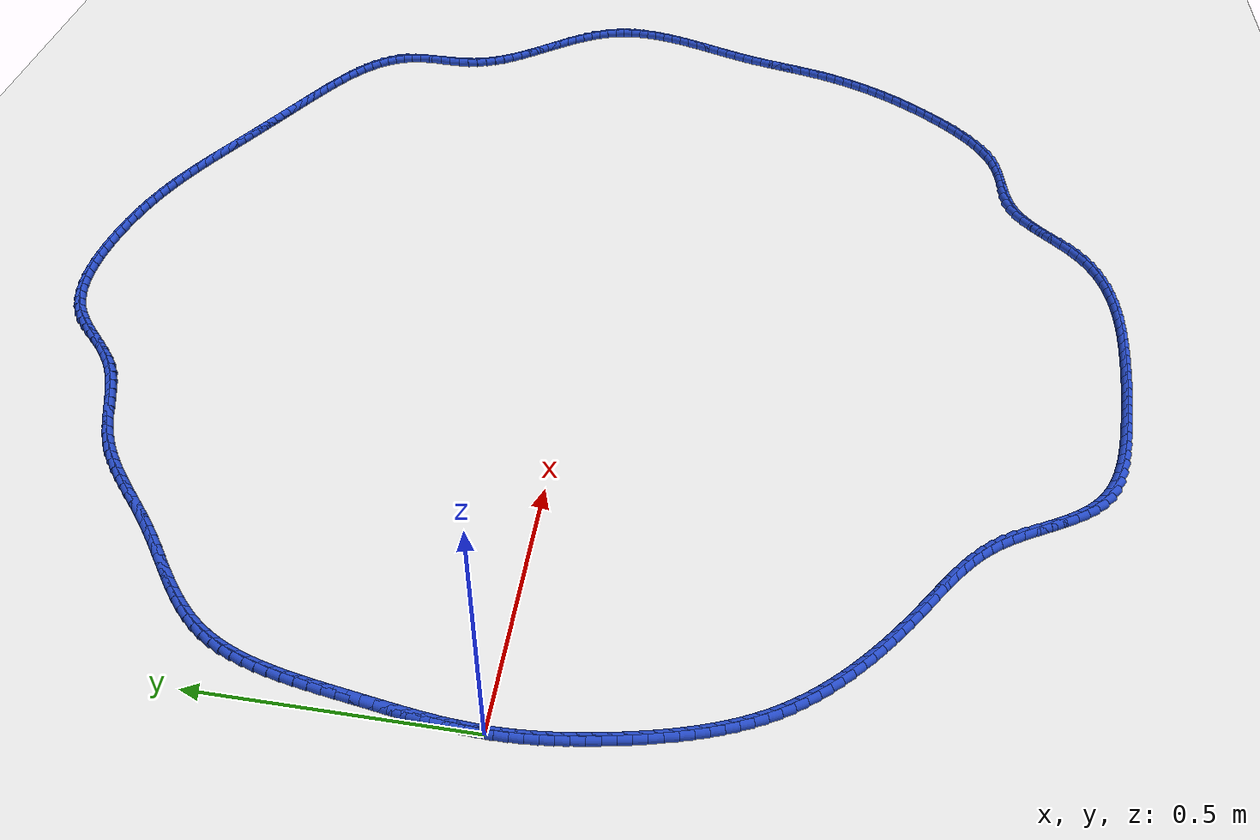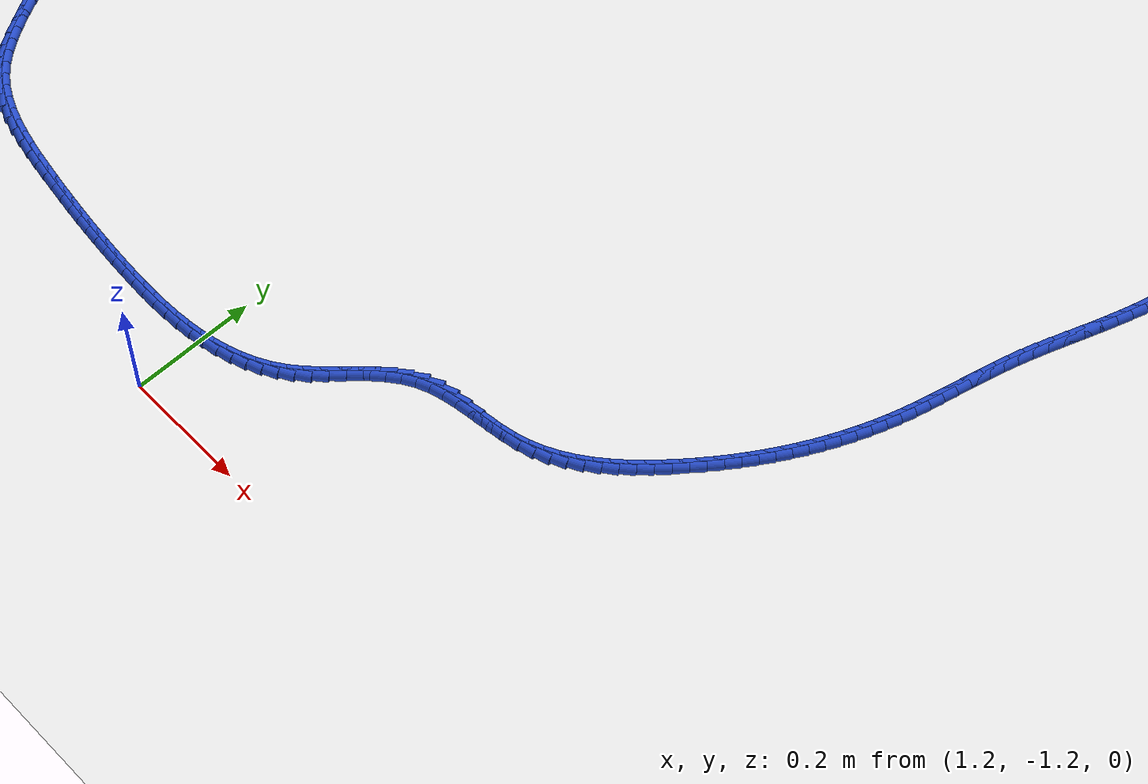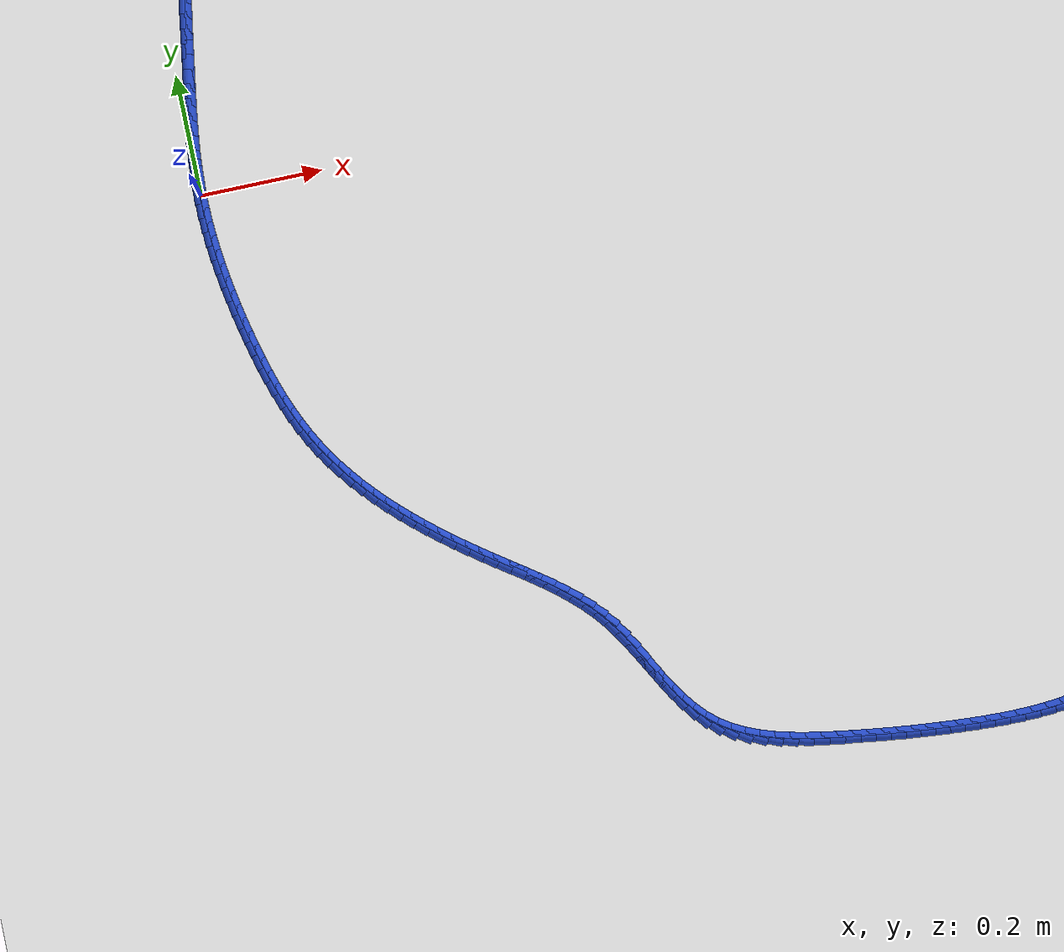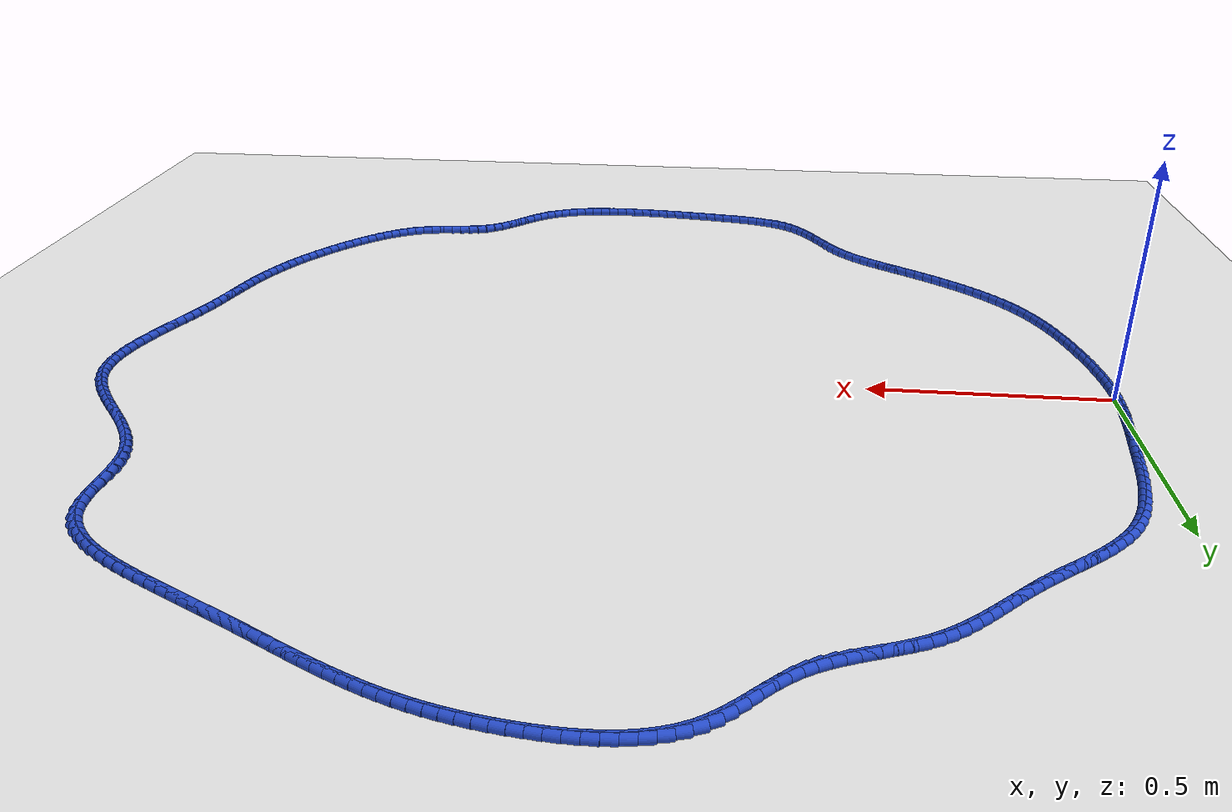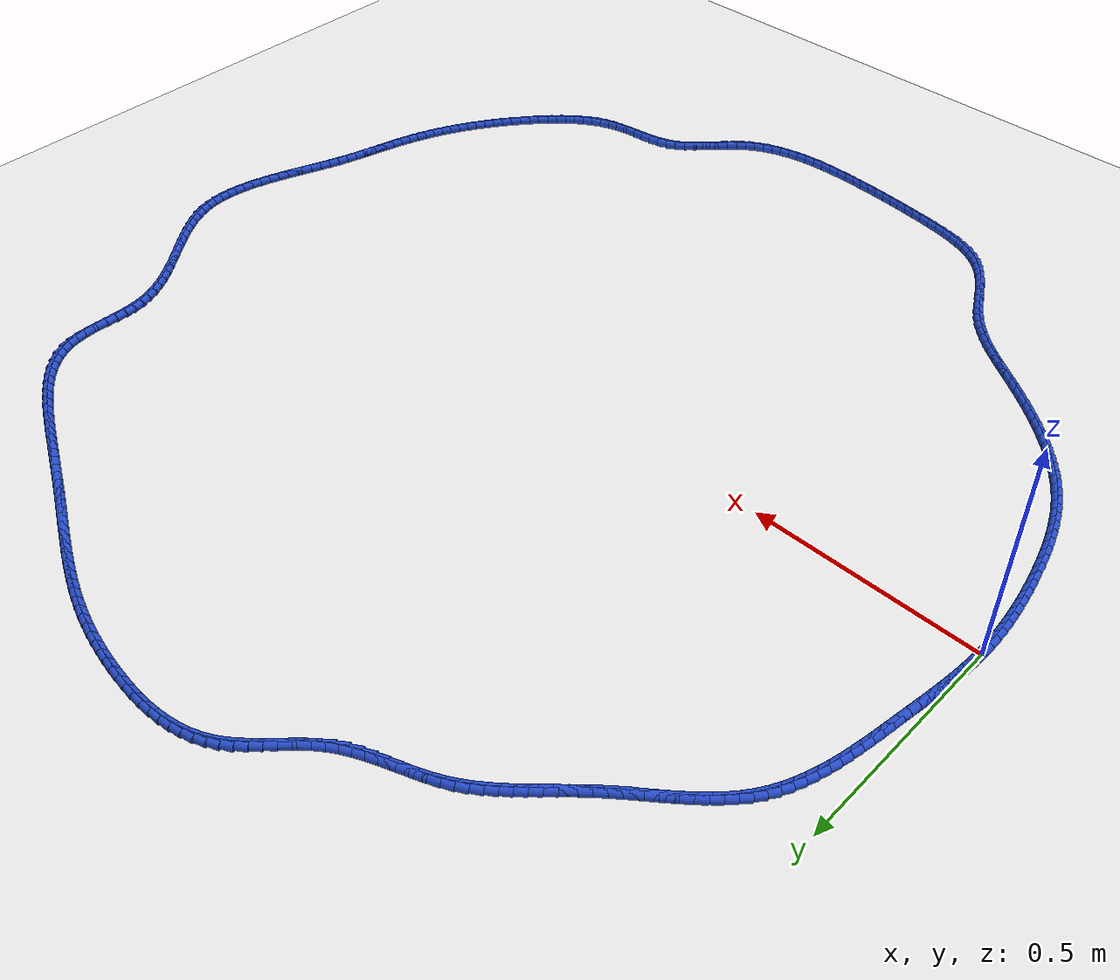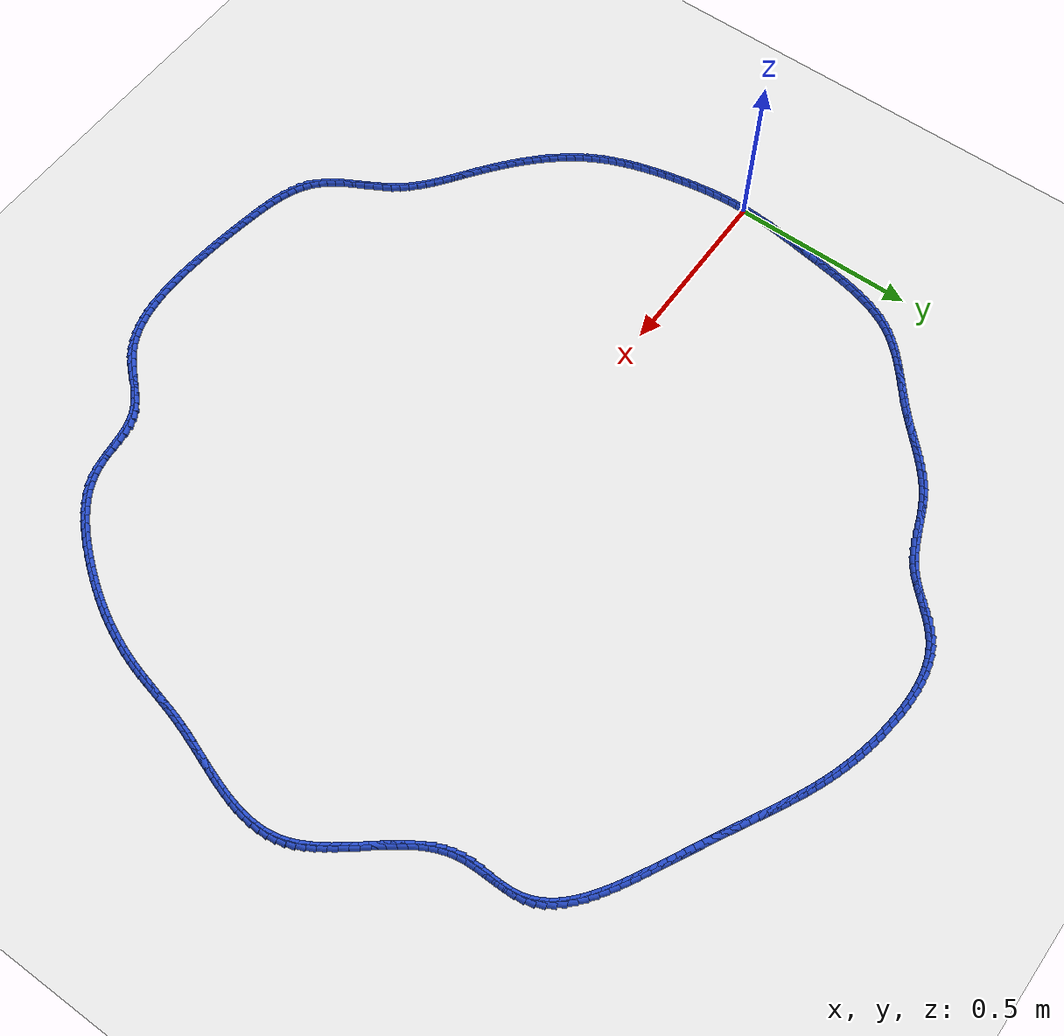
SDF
<sdf version="1.6">
 <world name="default">
  <light name="sun" type="directional">
   <pose>0 0 10 0 -0 0</pose>
   <diffuse>0.8 0.8 0.8 1</diffuse>
   <specular>0.2 0.2 0.2 1</specular>
   <attenuation>
    <range>1000</range>
    <constant>0.9</constant>
    <linear>0.01</linear>
    <quadratic>0.001</quadratic>
   </attenuation>
   <direction>-0.5 0.1 -0.9</direction>
  </light>
  <model name="ground_plane">
   <static>1</static>
   <link name="link">
    <collision name="collision">
     <geometry><plane><normal>0 0 1</normal><size>100 100</size></plane></geometry>
     <surface><friction><ode><mu>100</mu><mu2>50</mu2></ode></friction></surface>
    </collision>
    <visual name="visual">
     <cast_shadows>0</cast_shadows>
     <geometry><plane><normal>0 0 1</normal><size>100 100</size></plane></geometry>
     <material>
      <script><uri>file://media/materials/scripts/gazebo.material</uri><name>Gazebo/WhiteGlow</name></script>
     </material>
    </visual>
   </link>
  </model>
  <gravity>0 0 -9.8</gravity>
  <magnetic_field>6e-06 2.3e-05 -4.2e-05</magnetic_field>
  <atmosphere type="adiabatic"/>
  <physics name="default_physics" default="0" type="ode">
   <max_step_size>0.001</max_step_size>
   <real_time_factor>1</real_time_factor>
   <real_time_update_rate>1000</real_time_update_rate>
  </physics>
  <scene><ambient>0.4 0.4 0.4 1</ambient><background>0.7 0.7 0.7 1</background><shadows>1</shadows></scene>
  <spherical_coordinates>
   <surface_model>EARTH_WGS84</surface_model>
   <latitude_deg>0</latitude_deg>
   <longitude_deg>0</longitude_deg>
   <elevation>0</elevation>
   <heading_deg>0</heading_deg>
  </spherical_coordinates>
  <model name="line">
   <link name="link_0">
    <pose>-9.540979117872439e-18 2.0816681711721685e-17 0.01 0 1.57 1.5407770515693082</pose>
    <collision name="collision">
     <geometry><cylinder><radius>0.01</radius><length>0.08</length></cylinder></geometry>
    </collision>
    <visual name="visual">
     <material>
      <script><name>Gazebo/Blue</name><uri>file://media/materials/scripts/gazebo.material</uri></script>
     </material>
     <geometry><cylinder><radius>0.01</radius><length>0.08</length></cylinder></geometry>
    </visual>
   </link>
   <link name="link_1">
    <pose>0.0007039607350209209 0.023443246292247203 0.01 0 1.57 1.5119384216422107</pose>
    <collision name="collision">
     <geometry><cylinder><radius>0.01</radius><length>0.08</length></cylinder></geometry>
    </collision>
    <visual name="visual">
     <material>
      <script><name>Gazebo/Blue</name><uri>file://media/materials/scripts/gazebo.material</uri></script>
     </material>
     <geometry><cylinder><radius>0.01</radius><length>0.08</length></cylinder></geometry>
    </visual>
   </link>
   <link name="link_2">
    <pose>0.0020833381301156046 0.04685189779126154 0.01 0 1.57 1.4868486777520553</pose>
    <collision name="collision">
     <geometry><cylinder><radius>0.01</radius><length>0.08</length></cylinder></geometry>
    </collision>
    <visual name="visual">
     <material>
      <script><name>Gazebo/Blue</name><uri>file://media/materials/scripts/gazebo.material</uri></script>
     </material>
     <geometry><cylinder><radius>0.01</radius><length>0.08</length></cylinder></geometry>
    </visual>
   </link>
   <link name="link_3">
    <pose>0.004052448588189521 0.07025318096007596 0.01 0 1.57 1.4655910035733346</pose>
    <collision name="collision">
     <geometry><cylinder><radius>0.01</radius><length>0.08</length></cylinder></geometry>
    </collision>
    <visual name="visual">
     <material>
      <script><name>Gazebo/Blue</name><uri>file://media/materials/scripts/gazebo.material</uri></script>
     </material>
     <geometry><cylinder><radius>0.01</radius><length>0.08</length></cylinder></geometry>
    </visual>
   </link>
   <link name="link_4">
    <pose>0.006525608512148148 0.09367432226172344 0.01 0 1.57 1.4482039419232804</pose>
    <collision name="collision">
     <geometry><cylinder><radius>0.01</radius><length>0.08</length></cylinder></geometry>
    </collision>
    <visual name="visual">
     <material>
      <script><name>Gazebo/Blue</name><uri>file://media/materials/scripts/gazebo.material</uri></script>
     </material>
     <geometry><cylinder><radius>0.01</radius><length>0.08</length></cylinder></geometry>
    </visual>
   </link>
   <link name="link_5">
    <pose>0.009417134304896966 0.11714254815923696 0.01 0 1.57 1.434690596058609</pose>
    <collision name="collision">
     <geometry><cylinder><radius>0.01</radius><length>0.08</length></cylinder></geometry>
    </collision>
    <visual name="visual">
     <material>
      <script><name>Gazebo/Blue</name><uri>file://media/materials/scripts/gazebo.material</uri></script>
     </material>
     <geometry><cylinder><radius>0.01</radius><length>0.08</length></cylinder></geometry>
    </visual>
   </link>
   <link name="link_6">
    <pose>0.01264134236934146 0.14068508511564942 0.01 0 1.57 1.425026799253435</pose>
    <collision name="collision">
     <geometry><cylinder><radius>0.01</radius><length>0.08</length></cylinder></geometry>
    </collision>
    <visual name="visual">
     <material>
      <script><name>Gazebo/Blue</name><uri>file://media/materials/scripts/gazebo.material</uri></script>
     </material>
     <geometry><cylinder><radius>0.01</radius><length>0.08</length></cylinder></geometry>
    </visual>
   </link>
   <link name="link_7">
    <pose>0.016112549108387095 0.16432915959399383 0.01 0 1.57 1.4191678046188034</pose>
    <collision name="collision">
     <geometry><cylinder><radius>0.01</radius><length>0.08</length></cylinder></geometry>
    </collision>
    <visual name="visual">
     <material>
      <script><name>Gazebo/Blue</name><uri>file://media/materials/scripts/gazebo.material</uri></script>
     </material>
     <geometry><cylinder><radius>0.01</radius><length>0.08</length></cylinder></geometry>
    </visual>
   </link>
   <link name="link_8">
    <pose>0.019745070924939368 0.18810199805730313 0.01 0 1.57 1.4170532946250656</pose>
    <collision name="collision">
     <geometry><cylinder><radius>0.01</radius><length>0.08</length></cylinder></geometry>
    </collision>
    <visual name="visual">
     <material>
      <script><name>Gazebo/Blue</name><uri>file://media/materials/scripts/gazebo.material</uri></script>
     </material>
     <geometry><cylinder><radius>0.01</radius><length>0.08</length></cylinder></geometry>
    </visual>
   </link>
   <link name="link_9">
    <pose>0.023453224221903744 0.21203082696861025 0.01 0 1.57 1.4183336058897658</pose>
    <collision name="collision">
     <geometry><cylinder><radius>0.01</radius><length>0.08</length></cylinder></geometry>
    </collision>
    <visual name="visual">
     <material>
      <script><name>Gazebo/Blue</name><uri>file://media/materials/scripts/gazebo.material</uri></script>
     </material>
     <geometry><cylinder><radius>0.01</radius><length>0.08</length></cylinder></geometry>
    </visual>
   </link>
   <link name="link_10">
    <pose>0.027157594450842166 0.2361391668995262 0.01 0 1.57 1.4181682066567567</pose>
    <collision name="collision">
     <geometry><cylinder><radius>0.01</radius><length>0.08</length></cylinder></geometry>
    </collision>
    <visual name="visual">
     <material>
      <script><name>Gazebo/Blue</name><uri>file://media/materials/scripts/gazebo.material</uri></script>
     </material>
     <geometry><cylinder><radius>0.01</radius><length>0.08</length></cylinder></geometry>
    </visual>
   </link>
   <link name="link_11">
    <pose>0.03088739949409216 0.26038632134257494 0.01 0 1.57 1.4125491955962404</pose>
    <collision name="collision">
     <geometry><cylinder><radius>0.01</radius><length>0.08</length></cylinder></geometry>
    </collision>
    <visual name="visual">
     <material>
      <script><name>Gazebo/Blue</name><uri>file://media/materials/scripts/gazebo.material</uri></script>
     </material>
     <geometry><cylinder><radius>0.01</radius><length>0.08</length></cylinder></geometry>
    </visual>
   </link>
   <link name="link_12">
    <pose>0.03476378162770155 0.28467725351621387 0.01 0 1.57 1.4013418805655828</pose>
    <collision name="collision">
     <geometry><cylinder><radius>0.01</radius><length>0.08</length></cylinder></geometry>
    </collision>
    <visual name="visual">
     <material>
      <script><name>Gazebo/Blue</name><uri>file://media/materials/scripts/gazebo.material</uri></script>
     </material>
     <geometry><cylinder><radius>0.01</radius><length>0.08</length></cylinder></geometry>
    </visual>
   </link>
   <link name="link_13">
    <pose>0.03891078132629113 0.3089152133950223 0.01 0 1.57 1.3844414244940548</pose>
    <collision name="collision">
     <geometry><cylinder><radius>0.01</radius><length>0.08</length></cylinder></geometry>
    </collision>
    <visual name="visual">
     <material>
      <script><name>Gazebo/Blue</name><uri>file://media/materials/scripts/gazebo.material</uri></script>
     </material>
     <geometry><cylinder><radius>0.01</radius><length>0.08</length></cylinder></geometry>
    </visual>
   </link>
   <link name="link_14">
    <pose>0.04345243906448163 0.3330034509535796 0.01 0 1.57 1.3616524891348782</pose>
    <collision name="collision">
     <geometry><cylinder><radius>0.01</radius><length>0.08</length></cylinder></geometry>
    </collision>
    <visual name="visual">
     <material>
      <script><name>Gazebo/Blue</name><uri>file://media/materials/scripts/gazebo.material</uri></script>
     </material>
     <geometry><cylinder><radius>0.01</radius><length>0.08</length></cylinder></geometry>
    </visual>
   </link>
   <link name="link_15">
    <pose>0.048512795316893856 0.35684521616646536 0.01 0 1.57 1.3327000092562877</pose>
    <collision name="collision">
     <geometry><cylinder><radius>0.01</radius><length>0.08</length></cylinder></geometry>
    </collision>
    <visual name="visual">
     <material>
      <script><name>Gazebo/Blue</name><uri>file://media/materials/scripts/gazebo.material</uri></script>
     </material>
     <geometry><cylinder><radius>0.01</radius><length>0.08</length></cylinder></geometry>
    </visual>
   </link>
   <link name="link_16">
    <pose>0.05421589055814851 0.3803437590082587 0.01 0 1.57 1.2972458100620468</pose>
    <collision name="collision">
     <geometry><cylinder><radius>0.01</radius><length>0.08</length></cylinder></geometry>
    </collision>
    <visual name="visual">
     <material>
      <script><name>Gazebo/Blue</name><uri>file://media/materials/scripts/gazebo.material</uri></script>
     </material>
     <geometry><cylinder><radius>0.01</radius><length>0.08</length></cylinder></geometry>
    </visual>
   </link>
   <link name="link_17">
    <pose>0.06068576526286641 0.40340232945353915 0.01 0 1.57 1.2549149986245636</pose>
    <collision name="collision">
     <geometry><cylinder><radius>0.01</radius><length>0.08</length></cylinder></geometry>
    </collision>
    <visual name="visual">
     <material>
      <script><name>Gazebo/Blue</name><uri>file://media/materials/scripts/gazebo.material</uri></script>
     </material>
     <geometry><cylinder><radius>0.01</radius><length>0.08</length></cylinder></geometry>
    </visual>
   </link>
   <link name="link_18">
    <pose>0.06804645990566827 0.42592417747688605 0.01 0 1.57 1.205337002489549</pose>
    <collision name="collision">
     <geometry><cylinder><radius>0.01</radius><length>0.08</length></cylinder></geometry>
    </collision>
    <visual name="visual">
     <material>
      <script><name>Gazebo/Blue</name><uri>file://media/materials/scripts/gazebo.material</uri></script>
     </material>
     <geometry><cylinder><radius>0.01</radius><length>0.08</length></cylinder></geometry>
    </visual>
   </link>
   <link name="link_19">
    <pose>0.07642201496117487 0.4478125530528787 0.01 0 1.57 1.148206278163256</pose>
    <collision name="collision">
     <geometry><cylinder><radius>0.01</radius><length>0.08</length></cylinder></geometry>
    </collision>
    <visual name="visual">
     <material>
      <script><name>Gazebo/Blue</name><uri>file://media/materials/scripts/gazebo.material</uri></script>
     </material>
     <geometry><cylinder><radius>0.01</radius><length>0.08</length></cylinder></geometry>
    </visual>
   </link>
   <link name="link_20">
    <pose>0.085936470904007 0.46897070615609676 0.01 0 1.57 1.0833658826943948</pose>
    <collision name="collision">
     <geometry><cylinder><radius>0.01</radius><length>0.08</length></cylinder></geometry>
    </collision>
    <visual name="visual">
     <material>
      <script><name>Gazebo/Blue</name><uri>file://media/materials/scripts/gazebo.material</uri></script>
     </material>
     <geometry><cylinder><radius>0.01</radius><length>0.08</length></cylinder></geometry>
    </visual>
   </link>
   <link name="link_21">
    <pose>0.09671386820878536 0.48930188676111935 0.01 0 1.57 1.0109116515607788</pose>
    <collision name="collision">
     <geometry><cylinder><radius>0.01</radius><length>0.08</length></cylinder></geometry>
    </collision>
    <visual name="visual">
     <material>
      <script><name>Gazebo/Blue</name><uri>file://media/materials/scripts/gazebo.material</uri></script>
     </material>
     <geometry><cylinder><radius>0.01</radius><length>0.08</length></cylinder></geometry>
    </visual>
   </link>
   <link name="link_22">
    <pose>0.10887824735013077 0.508709344842526 0.01 0 1.57 0.9339457229736611</pose>
    <collision name="collision">
     <geometry><cylinder><radius>0.01</radius><length>0.08</length></cylinder></geometry>
    </collision>
    <visual name="visual">
     <material>
      <script><name>Gazebo/Blue</name><uri>file://media/materials/scripts/gazebo.material</uri></script>
     </material>
     <geometry><cylinder><radius>0.01</radius><length>0.08</length></cylinder></geometry>
    </visual>
   </link>
   <link name="link_23">
    <pose>0.12250541340928028 0.5271328987845552 0.01 0 1.57 0.8646154950748048</pose>
    <collision name="collision">
     <geometry><cylinder><radius>0.01</radius><length>0.08</length></cylinder></geometry>
    </collision>
    <visual name="visual">
     <material>
      <script><name>Gazebo/Blue</name><uri>file://media/materials/scripts/gazebo.material</uri></script>
     </material>
     <geometry><cylinder><radius>0.01</radius><length>0.08</length></cylinder></geometry>
    </visual>
   </link>
   <link name="link_24">
    <pose>0.13746308212700556 0.5446701244958287 0.01 0 1.57 0.80641069232532</pose>
    <collision name="collision">
     <geometry><cylinder><radius>0.01</radius><length>0.08</length></cylinder></geometry>
    </collision>
    <visual name="visual">
     <material>
      <script><name>Gazebo/Blue</name><uri>file://media/materials/scripts/gazebo.material</uri></script>
     </material>
     <geometry><cylinder><radius>0.01</radius><length>0.08</length></cylinder></geometry>
    </visual>
   </link>
   <link name="link_25">
    <pose>0.1535628673113773 0.5614611301069279 0.01 0 1.57 0.7592710794637001</pose>
    <collision name="collision">
     <geometry><cylinder><radius>0.01</radius><length>0.08</length></cylinder></geometry>
    </collision>
    <visual name="visual">
     <material>
      <script><name>Gazebo/Blue</name><uri>file://media/materials/scripts/gazebo.material</uri></script>
     </material>
     <geometry><cylinder><radius>0.01</radius><length>0.08</length></cylinder></geometry>
    </visual>
   </link>
   <link name="link_26">
    <pose>0.17061638193874673 0.5776460243789798 0.01 0 1.57 0.7228648250027255</pose>
    <collision name="collision">
     <geometry><cylinder><radius>0.01</radius><length>0.08</length></cylinder></geometry>
    </collision>
    <visual name="visual">
     <material>
      <script><name>Gazebo/Blue</name><uri>file://media/materials/scripts/gazebo.material</uri></script>
     </material>
     <geometry><cylinder><radius>0.01</radius><length>0.08</length></cylinder></geometry>
    </visual>
   </link>
   <link name="link_27">
    <pose>0.18843523898546488 0.5933649160731121 0.01 0 1.57 0.6967609345195616</pose>
    <collision name="collision">
     <geometry><cylinder><radius>0.01</radius><length>0.08</length></cylinder></geometry>
    </collision>
    <visual name="visual">
     <material>
      <script><name>Gazebo/Blue</name><uri>file://media/materials/scripts/gazebo.material</uri></script>
     </material>
     <geometry><cylinder><radius>0.01</radius><length>0.08</length></cylinder></geometry>
    </visual>
   </link>
   <link name="link_28">
    <pose>0.20683105142788316 0.6087579139504528 0.01 0 1.57 0.680547251542199</pose>
    <collision name="collision">
     <geometry><cylinder><radius>0.01</radius><length>0.08</length></cylinder></geometry>
    </collision>
    <visual name="visual">
     <material>
      <script><name>Gazebo/Blue</name><uri>file://media/materials/scripts/gazebo.material</uri></script>
     </material>
     <geometry><cylinder><radius>0.01</radius><length>0.08</length></cylinder></geometry>
    </visual>
   </link>
   <link name="link_29">
    <pose>0.22561543224235261 0.6239651267721288 0.01 0 1.57 0.6739016617673588</pose>
    <collision name="collision">
     <geometry><cylinder><radius>0.01</radius><length>0.08</length></cylinder></geometry>
    </collision>
    <visual name="visual">
     <material>
      <script><name>Gazebo/Blue</name><uri>file://media/materials/scripts/gazebo.material</uri></script>
     </material>
     <geometry><cylinder><radius>0.01</radius><length>0.08</length></cylinder></geometry>
    </visual>
   </link>
   <link name="link_30">
    <pose>0.24459999440522437 0.6391266632992677 0.01 0 1.57 0.6766281729278946</pose>
    <collision name="collision">
     <geometry><cylinder><radius>0.01</radius><length>0.08</length></cylinder></geometry>
    </collision>
    <visual name="visual">
     <material>
      <script><name>Gazebo/Blue</name><uri>file://media/materials/scripts/gazebo.material</uri></script>
     </material>
     <geometry><cylinder><radius>0.01</radius><length>0.08</length></cylinder></geometry>
    </visual>
   </link>
   <link name="link_31">
    <pose>0.2635963508928498 0.6543826322929973 0.01 0 1.57 0.6886672748198519</pose>
    <collision name="collision">
     <geometry><cylinder><radius>0.01</radius><length>0.08</length></cylinder></geometry>
    </collision>
    <visual name="visual">
     <material>
      <script><name>Gazebo/Blue</name><uri>file://media/materials/scripts/gazebo.material</uri></script>
     </material>
     <geometry><cylinder><radius>0.01</radius><length>0.08</length></cylinder></geometry>
    </visual>
   </link>
   <link name="link_32">
    <pose>0.28241611468157996 0.6698731425144453 0.01 0 1.57 0.7100357722436533</pose>
    <collision name="collision">
     <geometry><cylinder><radius>0.01</radius><length>0.08</length></cylinder></geometry>
    </collision>
    <visual name="visual">
     <material>
      <script><name>Gazebo/Blue</name><uri>file://media/materials/scripts/gazebo.material</uri></script>
     </material>
     <geometry><cylinder><radius>0.01</radius><length>0.08</length></cylinder></geometry>
    </visual>
   </link>
   <link name="link_33">
    <pose>0.3008717657688238 0.6857374516433993 0.01 0 1.57 0.7349222147536127</pose>
    <collision name="collision">
     <geometry><cylinder><radius>0.01</radius><length>0.08</length></cylinder></geometry>
    </collision>
    <visual name="visual">
     <material>
      <script><name>Gazebo/Blue</name><uri>file://media/materials/scripts/gazebo.material</uri></script>
     </material>
     <geometry><cylinder><radius>0.01</radius><length>0.08</length></cylinder></geometry>
    </visual>
   </link>
   <link name="link_34">
    <pose>0.31887938649303904 0.7020131196922386 0.01 0 1.57 0.7518350208697102</pose>
    <collision name="collision">
     <geometry><cylinder><radius>0.01</radius><length>0.08</length></cylinder></geometry>
    </collision>
    <visual name="visual">
     <material>
      <script><name>Gazebo/Blue</name><uri>file://media/materials/scripts/gazebo.material</uri></script>
     </material>
     <geometry><cylinder><radius>0.01</radius><length>0.08</length></cylinder></geometry>
    </visual>
   </link>
   <link name="link_35">
    <pose>0.3365555710719802 0.7185408810977232 0.01 0 1.57 0.7594019379892776</pose>
    <collision name="collision">
     <geometry><cylinder><radius>0.01</radius><length>0.08</length></cylinder></geometry>
    </collision>
    <visual name="visual">
     <material>
      <script><name>Gazebo/Blue</name><uri>file://media/materials/scripts/gazebo.material</uri></script>
     </material>
     <geometry><cylinder><radius>0.01</radius><length>0.08</length></cylinder></geometry>
    </visual>
   </link>
   <link name="link_36">
    <pose>0.3540398539644912 0.7351389517995893 0.01 0 1.57 0.7575350575067379</pose>
    <collision name="collision">
     <geometry><cylinder><radius>0.01</radius><length>0.08</length></cylinder></geometry>
    </collision>
    <visual name="visual">
     <material>
      <script><name>Gazebo/Blue</name><uri>file://media/materials/scripts/gazebo.material</uri></script>
     </material>
     <geometry><cylinder><radius>0.01</radius><length>0.08</length></cylinder></geometry>
    </visual>
   </link>
   <link name="link_37">
    <pose>0.3714717696294159 0.7516255477375732 0.01 0 1.57 0.7460932719653166</pose>
    <collision name="collision">
     <geometry><cylinder><radius>0.01</radius><length>0.08</length></cylinder></geometry>
    </collision>
    <visual name="visual">
     <material>
      <script><name>Gazebo/Blue</name><uri>file://media/materials/scripts/gazebo.material</uri></script>
     </material>
     <geometry><cylinder><radius>0.01</radius><length>0.08</length></cylinder></geometry>
    </visual>
   </link>
   <link name="link_38">
    <pose>0.3889908525255979 0.7678188848514105 0.01 0 1.57 0.72488506858001</pose>
    <collision name="collision">
     <geometry><cylinder><radius>0.01</radius><length>0.08</length></cylinder></geometry>
    </collision>
    <visual name="visual">
     <material>
      <script><name>Gazebo/Blue</name><uri>file://media/materials/scripts/gazebo.material</uri></script>
     </material>
     <geometry><cylinder><radius>0.01</radius><length>0.08</length></cylinder></geometry>
    </visual>
   </link>
   <link name="link_39">
    <pose>0.40673663711188124 0.7835371790808379 0.01 0 1.57 0.6936984867668919</pose>
    <collision name="collision">
     <geometry><cylinder><radius>0.01</radius><length>0.08</length></cylinder></geometry>
    </collision>
    <visual name="visual">
     <material>
      <script><name>Gazebo/Blue</name><uri>file://media/materials/scripts/gazebo.material</uri></script>
     </material>
     <geometry><cylinder><radius>0.01</radius><length>0.08</length></cylinder></geometry>
    </visual>
   </link>
   <link name="link_40">
    <pose>0.4248486578471094 0.7985986463655912 0.01 0 1.57 0.6523625248292201</pose>
    <collision name="collision">
     <geometry><cylinder><radius>0.01</radius><length>0.08</length></cylinder></geometry>
    </collision>
    <visual name="visual">
     <material>
      <script><name>Gazebo/Blue</name><uri>file://media/materials/scripts/gazebo.material</uri></script>
     </material>
     <geometry><cylinder><radius>0.01</radius><length>0.08</length></cylinder></geometry>
    </visual>
   </link>
   <link name="link_41">
    <pose>0.4434664491901267 0.8128215026454069 0.01 0 1.57 0.6008435266584947</pose>
    <collision name="collision">
     <geometry><cylinder><radius>0.01</radius><length>0.08</length></cylinder></geometry>
    </collision>
    <visual name="visual">
     <material>
      <script><name>Gazebo/Blue</name><uri>file://media/materials/scripts/gazebo.material</uri></script>
     </material>
     <geometry><cylinder><radius>0.01</radius><length>0.08</length></cylinder></geometry>
    </visual>
   </link>
   <link name="link_42">
    <pose>0.4627295455997763 0.8260239638600209 0.01 0 1.57 0.5393743097386239</pose>
    <collision name="collision">
     <geometry><cylinder><radius>0.01</radius><length>0.08</length></cylinder></geometry>
    </collision>
    <visual name="visual">
     <material>
      <script><name>Gazebo/Blue</name><uri>file://media/materials/scripts/gazebo.material</uri></script>
     </material>
     <geometry><cylinder><radius>0.01</radius><length>0.08</length></cylinder></geometry>
    </visual>
   </link>
   <link name="link_43">
    <pose>0.4827774815349023 0.8380242459491689 0.01 0 1.57 0.47217004068230733</pose>
    <collision name="collision">
     <geometry><cylinder><radius>0.01</radius><length>0.08</length></cylinder></geometry>
    </collision>
    <visual name="visual">
     <material>
      <script><name>Gazebo/Blue</name><uri>file://media/materials/scripts/gazebo.material</uri></script>
     </material>
     <geometry><cylinder><radius>0.01</radius><length>0.08</length></cylinder></geometry>
    </visual>
   </link>
   <link name="link_44">
    <pose>0.503702030063177 0.8487103896333908 0.01 0 1.57 0.4186377876868359</pose>
    <collision name="collision">
     <geometry><cylinder><radius>0.01</radius><length>0.08</length></cylinder></geometry>
    </collision>
    <visual name="visual">
     <material>
      <script><name>Gazebo/Blue</name><uri>file://media/materials/scripts/gazebo.material</uri></script>
     </material>
     <geometry><cylinder><radius>0.01</radius><length>0.08</length></cylinder></geometry>
    </visual>
   </link>
   <link name="link_45">
    <pose>0.5253427269471423 0.8583391940405665 0.01 0 1.57 0.384561296786893</pose>
    <collision name="collision">
     <geometry><cylinder><radius>0.01</radius><length>0.08</length></cylinder></geometry>
    </collision>
    <visual name="visual">
     <material>
      <script><name>Gazebo/Blue</name><uri>file://media/materials/scripts/gazebo.material</uri></script>
     </material>
     <geometry><cylinder><radius>0.01</radius><length>0.08</length></cylinder></geometry>
    </visual>
   </link>
   <link name="link_46">
    <pose>0.5474561450837011 0.8672887458860201 0.01 0 1.57 0.3693214571496849</pose>
    <collision name="collision">
     <geometry><cylinder><radius>0.01</radius><length>0.08</length></cylinder></geometry>
    </collision>
    <visual name="visual">
     <material>
      <script><name>Gazebo/Blue</name><uri>file://media/materials/scripts/gazebo.material</uri></script>
     </material>
     <geometry><cylinder><radius>0.01</radius><length>0.08</length></cylinder></geometry>
    </visual>
   </link>
   <link name="link_47">
    <pose>0.569798807389078 0.8759372049543415 0.01 0 1.57 0.37253379139638093</pose>
    <collision name="collision">
     <geometry><cylinder><radius>0.01</radius><length>0.08</length></cylinder></geometry>
    </collision>
    <visual name="visual">
     <material>
      <script><name>Gazebo/Blue</name><uri>file://media/materials/scripts/gazebo.material</uri></script>
     </material>
     <geometry><cylinder><radius>0.01</radius><length>0.08</length></cylinder></geometry>
    </visual>
   </link>
   <link name="link_48">
    <pose>0.5921272367794974 0.8846627310301204 0.01 0 1.57 0.39419719822216304</pose>
    <collision name="collision">
     <geometry><cylinder><radius>0.01</radius><length>0.08</length></cylinder></geometry>
    </collision>
    <visual name="visual">
     <material>
      <script><name>Gazebo/Blue</name><uri>file://media/materials/scripts/gazebo.material</uri></script>
     </material>
     <geometry><cylinder><radius>0.01</radius><length>0.08</length></cylinder></geometry>
    </visual>
   </link>
   <link name="link_49">
    <pose>0.6141979561711851 0.8938434838979471 0.01 0 1.57 0.4346592966926813</pose>
    <collision name="collision">
     <geometry><cylinder><radius>0.01</radius><length>0.08</length></cylinder></geometry>
    </collision>
    <visual name="visual">
     <material>
      <script><name>Gazebo/Blue</name><uri>file://media/materials/scripts/gazebo.material</uri></script>
     </material>
     <geometry><cylinder><radius>0.01</radius><length>0.08</length></cylinder></geometry>
    </visual>
   </link>
   <link name="link_50">
    <pose>0.6357674884803659 0.9038576233424114 0.01 0 1.57 0.4943989613907703</pose>
    <collision name="collision">
     <geometry><cylinder><radius>0.01</radius><length>0.08</length></cylinder></geometry>
    </collision>
    <visual name="visual">
     <material>
      <script><name>Gazebo/Blue</name><uri>file://media/materials/scripts/gazebo.material</uri></script>
     </material>
     <geometry><cylinder><radius>0.01</radius><length>0.08</length></cylinder></geometry>
    </visual>
   </link>
   <link name="link_51">
    <pose>0.6565923566232643 0.9150833091481029 0.01 0 1.57 0.5735758471489856</pose>
    <collision name="collision">
     <geometry><cylinder><radius>0.01</radius><length>0.08</length></cylinder></geometry>
    </collision>
    <visual name="visual">
     <material>
      <script><name>Gazebo/Blue</name><uri>file://media/materials/scripts/gazebo.material</uri></script>
     </material>
     <geometry><cylinder><radius>0.01</radius><length>0.08</length></cylinder></geometry>
    </visual>
   </link>
   <link name="link_52">
    <pose>0.6764292451110925 0.9278984372863254 0.01 0 1.57 0.6610452300955282</pose>
    <collision name="collision">
     <geometry><cylinder><radius>0.01</radius><length>0.08</length></cylinder></geometry>
    </collision>
    <visual name="visual">
     <material>
      <script><name>Gazebo/Blue</name><uri>file://media/materials/scripts/gazebo.material</uri></script>
     </material>
     <geometry><cylinder><radius>0.01</radius><length>0.08</length></cylinder></geometry>
    </visual>
   </link>
   <link name="link_53">
    <pose>0.6951640268208855 0.9424699961496759 0.01 0 1.57 0.7269939341002235</pose>
    <collision name="collision">
     <geometry><cylinder><radius>0.01</radius><length>0.08</length></cylinder></geometry>
    </collision>
    <visual name="visual">
     <material>
      <script><name>Gazebo/Blue</name><uri>file://media/materials/scripts/gazebo.material</uri></script>
     </material>
     <geometry><cylinder><radius>0.01</radius><length>0.08</length></cylinder></geometry>
    </visual>
   </link>
   <link name="link_54">
    <pose>0.7130441440453452 0.958374690868741 0.01 0 1.57 0.7670843107040698</pose>
    <collision name="collision">
     <geometry><cylinder><radius>0.01</radius><length>0.08</length></cylinder></geometry>
    </collision>
    <visual name="visual">
     <material>
      <script><name>Gazebo/Blue</name><uri>file://media/materials/scripts/gazebo.material</uri></script>
     </material>
     <geometry><cylinder><radius>0.01</radius><length>0.08</length></cylinder></geometry>
    </visual>
   </link>
   <link name="link_55">
    <pose>0.7303798127500479 0.9750867448740865 0.01 0 1.57 0.7822364435346553</pose>
    <collision name="collision">
     <geometry><cylinder><radius>0.01</radius><length>0.08</length></cylinder></geometry>
    </collision>
    <visual name="visual">
     <material>
      <script><name>Gazebo/Blue</name><uri>file://media/materials/scripts/gazebo.material</uri></script>
     </material>
     <geometry><cylinder><radius>0.01</radius><length>0.08</length></cylinder></geometry>
    </visual>
   </link>
   <link name="link_56">
    <pose>0.7474812489005696 0.9920803815962782 0.01 0 1.57 0.7727841471737972</pose>
    <collision name="collision">
     <geometry><cylinder><radius>0.01</radius><length>0.08</length></cylinder></geometry>
    </collision>
    <visual name="visual">
     <material>
      <script><name>Gazebo/Blue</name><uri>file://media/materials/scripts/gazebo.material</uri></script>
     </material>
     <geometry><cylinder><radius>0.01</radius><length>0.08</length></cylinder></geometry>
    </visual>
   </link>
   <link name="link_57">
    <pose>0.7646586684624863 1.0088298244658824 0.01 0 1.57 0.7382060223441684</pose>
    <collision name="collision">
     <geometry><cylinder><radius>0.01</radius><length>0.08</length></cylinder></geometry>
    </collision>
    <visual name="visual">
     <material>
      <script><name>Gazebo/Blue</name><uri>file://media/materials/scripts/gazebo.material</uri></script>
     </material>
     <geometry><cylinder><radius>0.01</radius><length>0.08</length></cylinder></geometry>
    </visual>
   </link>
   <link name="link_58">
    <pose>0.7822222874013742 1.0248092969134652 0.01 0 1.57 0.6772636147150964</pose>
    <collision name="collision">
     <geometry><cylinder><radius>0.01</radius><length>0.08</length></cylinder></geometry>
    </collision>
    <visual name="visual">
     <material>
      <script><name>Gazebo/Blue</name><uri>file://media/materials/scripts/gazebo.material</uri></script>
     </material>
     <geometry><cylinder><radius>0.01</radius><length>0.08</length></cylinder></geometry>
    </visual>
   </link>
   <link name="link_59">
    <pose>0.8004823216828095 1.0394930223695928 0.01 0 1.57 0.5886416760123346</pose>
    <collision name="collision">
     <geometry><cylinder><radius>0.01</radius><length>0.08</length></cylinder></geometry>
    </collision>
    <visual name="visual">
     <material>
      <script><name>Gazebo/Blue</name><uri>file://media/materials/scripts/gazebo.material</uri></script>
     </material>
     <geometry><cylinder><radius>0.01</radius><length>0.08</length></cylinder></geometry>
    </visual>
   </link>
   <link name="link_60">
    <pose>0.8197489710003054 1.0523552479648886 0.01 0 1.57 0.47943375359117796</pose>
    <collision name="collision">
     <geometry><cylinder><radius>0.01</radius><length>0.08</length></cylinder></geometry>
    </collision>
    <visual name="visual">
     <material>
      <script><name>Gazebo/Blue</name><uri>file://media/materials/scripts/gazebo.material</uri></script>
     </material>
     <geometry><cylinder><radius>0.01</radius><length>0.08</length></cylinder></geometry>
    </visual>
   </link>
   <link name="link_61">
    <pose>0.8402382265067176 1.0630074344011355 0.01 0 1.57 0.37527042201556676</pose>
    <collision name="collision">
     <geometry><cylinder><radius>0.01</radius><length>0.08</length></cylinder></geometry>
    </collision>
    <visual name="visual">
     <material>
      <script><name>Gazebo/Blue</name><uri>file://media/materials/scripts/gazebo.material</uri></script>
     </material>
     <geometry><cylinder><radius>0.01</radius><length>0.08</length></cylinder></geometry>
    </visual>
   </link>
   <link name="link_62">
    <pose>0.8618501376412108 1.07152120756802 0.01 0 1.57 0.2821956567172087</pose>
    <collision name="collision">
     <geometry><cylinder><radius>0.01</radius><length>0.08</length></cylinder></geometry>
    </collision>
    <visual name="visual">
     <material>
      <script><name>Gazebo/Blue</name><uri>file://media/materials/scripts/gazebo.material</uri></script>
     </material>
     <geometry><cylinder><radius>0.01</radius><length>0.08</length></cylinder></geometry>
    </visual>
   </link>
   <link name="link_63">
    <pose>0.8844185971976646 1.0780645496886567 0.01 0 1.57 0.20023888609111884</pose>
    <collision name="collision">
     <geometry><cylinder><radius>0.01</radius><length>0.08</length></cylinder></geometry>
    </collision>
    <visual name="visual">
     <material>
      <script><name>Gazebo/Blue</name><uri>file://media/materials/scripts/gazebo.material</uri></script>
     </material>
     <geometry><cylinder><radius>0.01</radius><length>0.08</length></cylinder></geometry>
    </visual>
   </link>
   <link name="link_64">
    <pose>0.9077774979699577 1.0828054429861602 0.01 0 1.57 0.12880779649803828</pose>
    <collision name="collision">
     <geometry><cylinder><radius>0.01</radius><length>0.08</length></cylinder></geometry>
    </collision>
    <visual name="visual">
     <material>
      <script><name>Gazebo/Blue</name><uri>file://media/materials/scripts/gazebo.material</uri></script>
     </material>
     <geometry><cylinder><radius>0.01</radius><length>0.08</length></cylinder></geometry>
    </visual>
   </link>
   <link name="link_65">
    <pose>0.9317607327519702 1.0859118696836458 0.01 0 1.57 0.06699631892306823</pose>
    <collision name="collision">
     <geometry><cylinder><radius>0.01</radius><length>0.08</length></cylinder></geometry>
    </collision>
    <visual name="visual">
     <material>
      <script><name>Gazebo/Blue</name><uri>file://media/materials/scripts/gazebo.material</uri></script>
     </material>
     <geometry><cylinder><radius>0.01</radius><length>0.08</length></cylinder></geometry>
    </visual>
   </link>
   <link name="link_66">
    <pose>0.9562021943375816 1.0875518120042293 0.01 0 1.57 0.0138038433373542</pose>
    <collision name="collision">
     <geometry><cylinder><radius>0.01</radius><length>0.08</length></cylinder></geometry>
    </collision>
    <visual name="visual">
     <material>
      <script><name>Gazebo/Blue</name><uri>file://media/materials/scripts/gazebo.material</uri></script>
     </material>
     <geometry><cylinder><radius>0.01</radius><length>0.08</length></cylinder></geometry>
    </visual>
   </link>
   <link name="link_67">
    <pose>0.9809357755206707 1.0878932521710243 0.01 0 1.57 -0.03173080513151163</pose>
    <collision name="collision">
     <geometry><cylinder><radius>0.01</radius><length>0.08</length></cylinder></geometry>
    </collision>
    <visual name="visual">
     <material>
      <script><name>Gazebo/Blue</name><uri>file://media/materials/scripts/gazebo.material</uri></script>
     </material>
     <geometry><cylinder><radius>0.01</radius><length>0.08</length></cylinder></geometry>
    </visual>
   </link>
   <link name="link_68">
    <pose>1.0057953690951176 1.0871041724071469 0.01 0 1.57 -0.07045742705025772</pose>
    <collision name="collision">
     <geometry><cylinder><radius>0.01</radius><length>0.08</length></cylinder></geometry>
    </collision>
    <visual name="visual">
     <material>
      <script><name>Gazebo/Blue</name><uri>file://media/materials/scripts/gazebo.material</uri></script>
     </material>
     <geometry><cylinder><radius>0.01</radius><length>0.08</length></cylinder></geometry>
    </visual>
   </link>
   <link name="link_69">
    <pose>1.030614867854801 1.0853525549357117 0.01 0 1.57 -0.10308039634264075</pose>
    <collision name="collision">
     <geometry><cylinder><radius>0.01</radius><length>0.08</length></cylinder></geometry>
    </collision>
    <visual name="visual">
     <material>
      <script><name>Gazebo/Blue</name><uri>file://media/materials/scripts/gazebo.material</uri></script>
     </material>
     <geometry><cylinder><radius>0.01</radius><length>0.08</length></cylinder></geometry>
    </visual>
   </link>
   <link name="link_70">
    <pose>1.055228164593601 1.0828063819798337 0.01 0 1.57 -0.13067224404088587</pose>
    <collision name="collision">
     <geometry><cylinder><radius>0.01</radius><length>0.08</length></cylinder></geometry>
    </collision>
    <visual name="visual">
     <material>
      <script><name>Gazebo/Blue</name><uri>file://media/materials/scripts/gazebo.material</uri></script>
     </material>
     <geometry><cylinder><radius>0.01</radius><length>0.08</length></cylinder></geometry>
    </visual>
   </link>
   <link name="link_71">
    <pose>1.0794861066105343 1.0796183762552884 0.01 0 1.57 -0.1573822876860002</pose>
    <collision name="collision">
     <geometry><cylinder><radius>0.01</radius><length>0.08</length></cylinder></geometry>
    </collision>
    <visual name="visual">
     <material>
      <script><name>Gazebo/Blue</name><uri>file://media/materials/scripts/gazebo.material</uri></script>
     </material>
     <geometry><cylinder><radius>0.01</radius><length>0.08</length></cylinder></geometry>
    </visual>
   </link>
   <link name="link_72">
    <pose>1.1033642201056064 1.0758290461378075 0.01 0 1.57 -0.1848736981832675</pose>
    <collision name="collision">
     <geometry><cylinder><radius>0.01</radius><length>0.08</length></cylinder></geometry>
    </collision>
    <visual name="visual">
     <material>
      <script><name>Gazebo/Blue</name><uri>file://media/materials/scripts/gazebo.material</uri></script>
     </material>
     <geometry><cylinder><radius>0.01</radius><length>0.08</length></cylinder></geometry>
    </visual>
   </link>
   <link name="link_73">
    <pose>1.1268936689105709 1.0714288246489243 0.01 0 1.57 -0.2130229744525341</pose>
    <collision name="collision">
     <geometry><cylinder><radius>0.01</radius><length>0.08</length></cylinder></geometry>
    </collision>
    <visual name="visual">
     <material>
      <script><name>Gazebo/Blue</name><uri>file://media/materials/scripts/gazebo.material</uri></script>
     </material>
     <geometry><cylinder><radius>0.01</radius><length>0.08</length></cylinder></geometry>
    </visual>
   </link>
   <link name="link_74">
    <pose>1.1501058741158405 1.0664079132705104 0.01 0 1.57 -0.24168375244150964</pose>
    <collision name="collision">
     <geometry><cylinder><radius>0.01</radius><length>0.08</length></cylinder></geometry>
    </collision>
    <visual name="visual">
     <material>
      <script><name>Gazebo/Blue</name><uri>file://media/materials/scripts/gazebo.material</uri></script>
     </material>
     <geometry><cylinder><radius>0.01</radius><length>0.08</length></cylinder></geometry>
    </visual>
   </link>
   <link name="link_75">
    <pose>1.1730322568118279 1.0607565134844348 0.01 0 1.57 -0.2706976305709654</pose>
    <collision name="collision">
     <geometry><cylinder><radius>0.01</radius><length>0.08</length></cylinder></geometry>
    </collision>
    <visual name="visual">
     <material>
      <script><name>Gazebo/Blue</name><uri>file://media/materials/scripts/gazebo.material</uri></script>
     </material>
     <geometry><cylinder><radius>0.01</radius><length>0.08</length></cylinder></geometry>
    </visual>
   </link>
   <link name="link_76">
    <pose>1.1957042380889469 1.054464826772568 0.01 0 1.57 -0.2998976431099499</pose>
    <collision name="collision">
     <geometry><cylinder><radius>0.01</radius><length>0.08</length></cylinder></geometry>
    </collision>
    <visual name="visual">
     <material>
      <script><name>Gazebo/Blue</name><uri>file://media/materials/scripts/gazebo.material</uri></script>
     </material>
     <geometry><cylinder><radius>0.01</radius><length>0.08</length></cylinder></geometry>
    </visual>
   </link>
   <link name="link_77">
    <pose>1.2181532390376104 1.047523054616781 0.01 0 1.57 -0.3291122250069193</pose>
    <collision name="collision">
     <geometry><cylinder><radius>0.01</radius><length>0.08</length></cylinder></geometry>
    </collision>
    <visual name="visual">
     <material>
      <script><name>Gazebo/Blue</name><uri>file://media/materials/scripts/gazebo.material</uri></script>
     </material>
     <geometry><cylinder><radius>0.01</radius><length>0.08</length></cylinder></geometry>
    </visual>
   </link>
   <link name="link_78">
    <pose>1.2404106807482318 1.039921398498943 0.01 0 1.57 -0.3579810117943625</pose>
    <collision name="collision">
     <geometry><cylinder><radius>0.01</radius><length>0.08</length></cylinder></geometry>
    </collision>
    <visual name="visual">
     <material>
      <script><name>Gazebo/Blue</name><uri>file://media/materials/scripts/gazebo.material</uri></script>
     </material>
     <geometry><cylinder><radius>0.01</radius><length>0.08</length></cylinder></geometry>
    </visual>
   </link>
   <link name="link_79">
    <pose>1.2625063422962612 1.0316554211861397 0.01 0 1.57 -0.3845879496227477</pose>
    <collision name="collision">
     <geometry><cylinder><radius>0.01</radius><length>0.08</length></cylinder></geometry>
    </collision>
    <visual name="visual">
     <material>
      <script><name>Gazebo/Blue</name><uri>file://media/materials/scripts/gazebo.material</uri></script>
     </material>
     <geometry><cylinder><radius>0.01</radius><length>0.08</length></cylinder></geometry>
    </visual>
   </link>
   <link name="link_80">
    <pose>1.2844542313718497 1.0227721800400509 0.01 0 1.57 -0.4079715077755365</pose>
    <collision name="collision">
     <geometry><cylinder><radius>0.01</radius><length>0.08</length></cylinder></geometry>
    </collision>
    <visual name="visual">
     <material>
      <script><name>Gazebo/Blue</name><uri>file://media/materials/scripts/gazebo.material</uri></script>
     </material>
     <geometry><cylinder><radius>0.01</radius><length>0.08</length></cylinder></geometry>
    </visual>
   </link>
   <link name="link_81">
    <pose>1.3062595620316726 1.013347444205263 0.01 0 1.57 -0.42819871986005664</pose>
    <collision name="collision">
     <geometry><cylinder><radius>0.01</radius><length>0.08</length></cylinder></geometry>
    </collision>
    <visual name="visual">
     <material>
      <script><name>Gazebo/Blue</name><uri>file://media/materials/scripts/gazebo.material</uri></script>
     </material>
     <geometry><cylinder><radius>0.01</radius><length>0.08</length></cylinder></geometry>
    </visual>
   </link>
   <link name="link_82">
    <pose>1.327927452973547 1.0034572941792115 0.01 0 1.57 -0.44534429112639395</pose>
    <collision name="collision">
     <geometry><cylinder><radius>0.01</radius><length>0.08</length></cylinder></geometry>
    </collision>
    <visual name="visual">
     <material>
      <script><name>Gazebo/Blue</name><uri>file://media/materials/scripts/gazebo.material</uri></script>
     </material>
     <geometry><cylinder><radius>0.01</radius><length>0.08</length></cylinder></geometry>
    </visual>
   </link>
   <link name="link_83">
    <pose>1.3494630228952884 0.9931778104593326 0.01 0 1.57 -0.4594743329119818</pose>
    <collision name="collision">
     <geometry><cylinder><radius>0.01</radius><length>0.08</length></cylinder></geometry>
    </collision>
    <visual name="visual">
     <material>
      <script><name>Gazebo/Blue</name><uri>file://media/materials/scripts/gazebo.material</uri></script>
     </material>
     <geometry><cylinder><radius>0.01</radius><length>0.08</length></cylinder></geometry>
    </visual>
   </link>
   <link name="link_84">
    <pose>1.370871390494715 0.9825850735430625 0.01 0 1.57 -0.4706422126383588</pose>
    <collision name="collision">
     <geometry><cylinder><radius>0.01</radius><length>0.08</length></cylinder></geometry>
    </collision>
    <visual name="visual">
     <material>
      <script><name>Gazebo/Blue</name><uri>file://media/materials/scripts/gazebo.material</uri></script>
     </material>
     <geometry><cylinder><radius>0.01</radius><length>0.08</length></cylinder></geometry>
    </visual>
   </link>
   <link name="link_85">
    <pose>1.3921576744696431 0.9717551639278366 0.01 0 1.57 -0.4788853208453655</pose>
    <collision name="collision">
     <geometry><cylinder><radius>0.01</radius><length>0.08</length></cylinder></geometry>
    </collision>
    <visual name="visual">
     <material>
      <script><name>Gazebo/Blue</name><uri>file://media/materials/scripts/gazebo.material</uri></script>
     </material>
     <geometry><cylinder><radius>0.01</radius><length>0.08</length></cylinder></geometry>
    </visual>
   </link>
   <link name="link_86">
    <pose>1.4133269935178896 0.9607641621110911 0.01 0 1.57 -0.48422252969457497</pose>
    <collision name="collision">
     <geometry><cylinder><radius>0.01</radius><length>0.08</length></cylinder></geometry>
    </collision>
    <visual name="visual">
     <material>
      <script><name>Gazebo/Blue</name><uri>file://media/materials/scripts/gazebo.material</uri></script>
     </material>
     <geometry><cylinder><radius>0.01</radius><length>0.08</length></cylinder></geometry>
    </visual>
   </link>
   <link name="link_87">
    <pose>1.4343844663372718 0.9496881485902615 0.01 0 1.57 -0.486652158961907</pose>
    <collision name="collision">
     <geometry><cylinder><radius>0.01</radius><length>0.08</length></cylinder></geometry>
    </collision>
    <visual name="visual">
     <material>
      <script><name>Gazebo/Blue</name><uri>file://media/materials/scripts/gazebo.material</uri></script>
     </material>
     <geometry><cylinder><radius>0.01</radius><length>0.08</length></cylinder></geometry>
    </visual>
   </link>
   <link name="link_88">
    <pose>1.4553352116256055 0.9386032038627843 0.01 0 1.57 -0.4861503142742502</pose>
    <collision name="collision">
     <geometry><cylinder><radius>0.01</radius><length>0.08</length></cylinder></geometry>
    </collision>
    <visual name="visual">
     <material>
      <script><name>Gazebo/Blue</name><uri>file://media/materials/scripts/gazebo.material</uri></script>
     </material>
     <geometry><cylinder><radius>0.01</radius><length>0.08</length></cylinder></geometry>
    </visual>
   </link>
   <link name="link_89">
    <pose>1.4761843480807075 0.9275854084260948 0.01 0 1.57 -0.4826882785012151</pose>
    <collision name="collision">
     <geometry><cylinder><radius>0.01</radius><length>0.08</length></cylinder></geometry>
    </collision>
    <visual name="visual">
     <material>
      <script><name>Gazebo/Blue</name><uri>file://media/materials/scripts/gazebo.material</uri></script>
     </material>
     <geometry><cylinder><radius>0.01</radius><length>0.08</length></cylinder></geometry>
    </visual>
   </link>
   <link name="link_90">
    <pose>1.4969372574148807 0.9167102086545844 0.01 0 1.57 -0.47767256656146895</pose>
    <collision name="collision">
     <geometry><cylinder><radius>0.01</radius><length>0.08</length></cylinder></geometry>
    </collision>
    <visual name="visual">
     <material>
      <script><name>Gazebo/Blue</name><uri>file://media/materials/scripts/gazebo.material</uri></script>
     </material>
     <geometry><cylinder><radius>0.01</radius><length>0.08</length></cylinder></geometry>
    </visual>
   </link>
   <link name="link_91">
    <pose>1.517619754757472 0.9060037863330029 0.01 0 1.57 -0.47361228682369366</pose>
    <collision name="collision">
     <geometry><cylinder><radius>0.01</radius><length>0.08</length></cylinder></geometry>
    </collision>
    <visual name="visual">
     <material>
      <script><name>Gazebo/Blue</name><uri>file://media/materials/scripts/gazebo.material</uri></script>
     </material>
     <geometry><cylinder><radius>0.01</radius><length>0.08</length></cylinder></geometry>
    </visual>
   </link>
   <link name="link_92">
    <pose>1.5382923388086174 0.8954087018000148 0.01 0 1.57 -0.47080228725001194</pose>
    <collision name="collision">
     <geometry><cylinder><radius>0.01</radius><length>0.08</length></cylinder></geometry>
    </collision>
    <visual name="visual">
     <material>
      <script><name>Gazebo/Blue</name><uri>file://media/materials/scripts/gazebo.material</uri></script>
     </material>
     <geometry><cylinder><radius>0.01</radius><length>0.08</length></cylinder></geometry>
    </visual>
   </link>
   <link name="link_93">
    <pose>1.5590188738765731 0.8848594009755051 0.01 0 1.57 -0.46926952690748897</pose>
    <collision name="collision">
     <geometry><cylinder><radius>0.01</radius><length>0.08</length></cylinder></geometry>
    </collision>
    <visual name="visual">
     <material>
      <script><name>Gazebo/Blue</name><uri>file://media/materials/scripts/gazebo.material</uri></script>
     </material>
     <geometry><cylinder><radius>0.01</radius><length>0.08</length></cylinder></geometry>
    </visual>
   </link>
   <link name="link_94">
    <pose>1.5798632242695962 0.8742903297793588 0.01 0 1.57 -0.46901238932947853</pose>
    <collision name="collision">
     <geometry><cylinder><radius>0.01</radius><length>0.08</length></cylinder></geometry>
    </collision>
    <visual name="visual">
     <material>
      <script><name>Gazebo/Blue</name><uri>file://media/materials/scripts/gazebo.material</uri></script>
     </material>
     <geometry><cylinder><radius>0.01</radius><length>0.08</length></cylinder></geometry>
    </visual>
   </link>
   <link name="link_95">
    <pose>1.6008892542959439 0.8636359341314617 0.01 0 1.57 -0.4700014957038165</pose>
    <collision name="collision">
     <geometry><cylinder><radius>0.01</radius><length>0.08</length></cylinder></geometry>
    </collision>
    <visual name="visual">
     <material>
      <script><name>Gazebo/Blue</name><uri>file://media/materials/scripts/gazebo.material</uri></script>
     </material>
     <geometry><cylinder><radius>0.01</radius><length>0.08</length></cylinder></geometry>
    </visual>
   </link>
   <link name="link_96">
    <pose>1.6221608282638722 0.8528306599516992 0.01 0 1.57 -0.4721819169983937</pose>
    <collision name="collision">
     <geometry><cylinder><radius>0.01</radius><length>0.08</length></cylinder></geometry>
    </collision>
    <visual name="visual">
     <material>
      <script><name>Gazebo/Blue</name><uri>file://media/materials/scripts/gazebo.material</uri></script>
     </material>
     <geometry><cylinder><radius>0.01</radius><length>0.08</length></cylinder></geometry>
    </visual>
   </link>
   <link name="link_97">
    <pose>1.643741810481637 0.8418089531599565 0.01 0 1.57 -0.47547654703833636</pose>
    <collision name="collision">
     <geometry><cylinder><radius>0.01</radius><length>0.08</length></cylinder></geometry>
    </collision>
    <visual name="visual">
     <material>
      <script><name>Gazebo/Blue</name><uri>file://media/materials/scripts/gazebo.material</uri></script>
     </material>
     <geometry><cylinder><radius>0.01</radius><length>0.08</length></cylinder></geometry>
    </visual>
   </link>
   <link name="link_98">
    <pose>1.665696065257497 0.8305052596761192 0.01 0 1.57 -0.4801085992604505</pose>
    <collision name="collision">
     <geometry><cylinder><radius>0.01</radius><length>0.08</length></cylinder></geometry>
    </collision>
    <visual name="visual">
     <material>
      <script><name>Gazebo/Blue</name><uri>file://media/materials/scripts/gazebo.material</uri></script>
     </material>
     <geometry><cylinder><radius>0.01</radius><length>0.08</length></cylinder></geometry>
    </visual>
   </link>
   <link name="link_99">
    <pose>1.6880708013147874 0.8188536408103001 0.01 0 1.57 -0.4898097105034367</pose>
    <collision name="collision">
     <geometry><cylinder><radius>0.01</radius><length>0.08</length></cylinder></geometry>
    </collision>
    <visual name="visual">
     <material>
      <script><name>Gazebo/Blue</name><uri>file://media/materials/scripts/gazebo.material</uri></script>
     </material>
     <geometry><cylinder><radius>0.01</radius><length>0.08</length></cylinder></geometry>
    </visual>
   </link>
   <link name="link_100">
    <pose>1.710710411162608 0.8067834744527079 0.01 0 1.57 -0.5070779755820154</pose>
    <collision name="collision">
     <geometry><cylinder><radius>0.01</radius><length>0.08</length></cylinder></geometry>
    </collision>
    <visual name="visual">
     <material>
      <script><name>Gazebo/Blue</name><uri>file://media/materials/scripts/gazebo.material</uri></script>
     </material>
     <geometry><cylinder><radius>0.01</radius><length>0.08</length></cylinder></geometry>
    </visual>
   </link>
   <link name="link_101">
    <pose>1.7333239353635435 0.7942210129544869 0.01 0 1.57 -0.5322050170920408</pose>
    <collision name="collision">
     <geometry><cylinder><radius>0.01</radius><length>0.08</length></cylinder></geometry>
    </collision>
    <visual name="visual">
     <material>
      <script><name>Gazebo/Blue</name><uri>file://media/materials/scripts/gazebo.material</uri></script>
     </material>
     <geometry><cylinder><radius>0.01</radius><length>0.08</length></cylinder></geometry>
    </visual>
   </link>
   <link name="link_102">
    <pose>1.7556179474072195 0.7810924516972796 0.01 0 1.57 -0.5657903739170047</pose>
    <collision name="collision">
     <geometry><cylinder><radius>0.01</radius><length>0.08</length></cylinder></geometry>
    </collision>
    <visual name="visual">
     <material>
      <script><name>Gazebo/Blue</name><uri>file://media/materials/scripts/gazebo.material</uri></script>
     </material>
     <geometry><cylinder><radius>0.01</radius><length>0.08</length></cylinder></geometry>
    </visual>
   </link>
   <link name="link_103">
    <pose>1.777299020783261 0.7673239860627287 0.01 0 1.57 -0.6087810697079531</pose>
    <collision name="collision">
     <geometry><cylinder><radius>0.01</radius><length>0.08</length></cylinder></geometry>
    </collision>
    <visual name="visual">
     <material>
      <script><name>Gazebo/Blue</name><uri>file://media/materials/scripts/gazebo.material</uri></script>
     </material>
     <geometry><cylinder><radius>0.01</radius><length>0.08</length></cylinder></geometry>
    </visual>
   </link>
   <link name="link_104">
    <pose>1.798073728981295 0.752841811432477 0.01 0 1.57 -0.6624661018655867</pose>
    <collision name="collision">
     <geometry><cylinder><radius>0.01</radius><length>0.08</length></cylinder></geometry>
    </collision>
    <visual name="visual">
     <material>
      <script><name>Gazebo/Blue</name><uri>file://media/materials/scripts/gazebo.material</uri></script>
     </material>
     <geometry><cylinder><radius>0.01</radius><length>0.08</length></cylinder></geometry>
    </visual>
   </link>
   <link name="link_105">
    <pose>1.8176486454909444 0.7375721231881673 0.01 0 1.57 -0.7284432359673142</pose>
    <collision name="collision">
     <geometry><cylinder><radius>0.01</radius><length>0.08</length></cylinder></geometry>
    </collision>
    <visual name="visual">
     <material>
      <script><name>Gazebo/Blue</name><uri>file://media/materials/scripts/gazebo.material</uri></script>
     </material>
     <geometry><cylinder><radius>0.01</radius><length>0.08</length></cylinder></geometry>
    </visual>
   </link>
   <link name="link_106">
    <pose>1.835730343801836 0.7214411167114424 0.01 0 1.57 -0.8085070101723594</pose>
    <collision name="collision">
     <geometry><cylinder><radius>0.01</radius><length>0.08</length></cylinder></geometry>
    </collision>
    <visual name="visual">
     <material>
      <script><name>Gazebo/Blue</name><uri>file://media/materials/scripts/gazebo.material</uri></script>
     </material>
     <geometry><cylinder><radius>0.01</radius><length>0.08</length></cylinder></geometry>
    </visual>
   </link>
   <link name="link_107">
    <pose>1.8520253974035938 0.7043749873839448 0.01 0 1.57 -0.9043773542919071</pose>
    <collision name="collision">
     <geometry><cylinder><radius>0.01</radius><length>0.08</length></cylinder></geometry>
    </collision>
    <visual name="visual">
     <material>
      <script><name>Gazebo/Blue</name><uri>file://media/materials/scripts/gazebo.material</uri></script>
     </material>
     <geometry><cylinder><radius>0.01</radius><length>0.08</length></cylinder></geometry>
    </visual>
   </link>
   <link name="link_108">
    <pose>1.8662403797858444 0.6862999305873175 0.01 0 1.57 -1.017172112886572</pose>
    <collision name="collision">
     <geometry><cylinder><radius>0.01</radius><length>0.08</length></cylinder></geometry>
    </collision>
    <visual name="visual">
     <material>
      <script><name>Gazebo/Blue</name><uri>file://media/materials/scripts/gazebo.material</uri></script>
     </material>
     <geometry><cylinder><radius>0.01</radius><length>0.08</length></cylinder></geometry>
    </visual>
   </link>
   <link name="link_109">
    <pose>1.8780818644382127 0.6671421417032027 0.01 0 1.57 -1.1465876552561638</pose>
    <collision name="collision">
     <geometry><cylinder><radius>0.01</radius><length>0.08</length></cylinder></geometry>
    </collision>
    <visual name="visual">
     <material>
      <script><name>Gazebo/Blue</name><uri>file://media/materials/scripts/gazebo.material</uri></script>
     </material>
     <geometry><cylinder><radius>0.01</radius><length>0.08</length></cylinder></geometry>
    </visual>
   </link>
   <link name="link_110">
    <pose>1.8872564248503232 0.6468278161132437 0.01 0 1.57 -1.2894282790665088</pose>
    <collision name="collision">
     <geometry><cylinder><radius>0.01</radius><length>0.08</length></cylinder></geometry>
    </collision>
    <visual name="visual">
     <material>
      <script><name>Gazebo/Blue</name><uri>file://media/materials/scripts/gazebo.material</uri></script>
     </material>
     <geometry><cylinder><radius>0.01</radius><length>0.08</length></cylinder></geometry>
    </visual>
   </link>
   <link name="link_111">
    <pose>1.893482434635169 0.6252872187120085 0.01 0 1.57 -1.4202013386655299</pose>
    <collision name="collision">
     <geometry><cylinder><radius>0.01</radius><length>0.08</length></cylinder></geometry>
    </collision>
    <visual name="visual">
     <material>
      <script><name>Gazebo/Blue</name><uri>file://media/materials/scripts/gazebo.material</uri></script>
     </material>
     <geometry><cylinder><radius>0.01</radius><length>0.08</length></cylinder></geometry>
    </visual>
   </link>
   <link name="link_112">
    <pose>1.8969244018434932 0.6026044729431993 0.01 0 1.57 -1.5116219188461573</pose>
    <collision name="collision">
     <geometry><cylinder><radius>0.01</radius><length>0.08</length></cylinder></geometry>
    </collision>
    <visual name="visual">
     <material>
      <script><name>Gazebo/Blue</name><uri>file://media/materials/scripts/gazebo.material</uri></script>
     </material>
     <geometry><cylinder><radius>0.01</radius><length>0.08</length></cylinder></geometry>
    </visual>
   </link>
   <link name="link_113">
    <pose>1.8983191958189813 0.5790610927020531 0.01 0 1.57 -1.565734980175591</pose>
    <collision name="collision">
     <geometry><cylinder><radius>0.01</radius><length>0.08</length></cylinder></geometry>
    </collision>
    <visual name="visual">
     <material>
      <script><name>Gazebo/Blue</name><uri>file://media/materials/scripts/gazebo.material</uri></script>
     </material>
     <geometry><cylinder><radius>0.01</radius><length>0.08</length></cylinder></geometry>
    </visual>
   </link>
   <link name="link_114">
    <pose>1.8984412236764558 0.5549515375488724 0.01 0 1.57 1.5553622966730036</pose>
    <collision name="collision">
     <geometry><cylinder><radius>0.01</radius><length>0.08</length></cylinder></geometry>
    </collision>
    <visual name="visual">
     <material>
      <script><name>Gazebo/Blue</name><uri>file://media/materials/scripts/gazebo.material</uri></script>
     </material>
     <geometry><cylinder><radius>0.01</radius><length>0.08</length></cylinder></geometry>
    </visual>
   </link>
   <link name="link_115">
    <pose>1.8980648925307406 0.5305702670439589 0.01 0 1.57 1.5666793918748065</pose>
    <collision name="collision">
     <geometry><cylinder><radius>0.01</radius><length>0.08</length></cylinder></geometry>
    </collision>
    <visual name="visual">
     <material>
      <script><name>Gazebo/Blue</name><uri>file://media/materials/scripts/gazebo.material</uri></script>
     </material>
     <geometry><cylinder><radius>0.01</radius><length>0.08</length></cylinder></geometry>
    </visual>
   </link>
   <link name="link_116">
    <pose>1.8979646094966578 0.5062117407476143 0.01 0 1.57 -1.5312944265313155</pose>
    <collision name="collision">
     <geometry><cylinder><radius>0.01</radius><length>0.08</length></cylinder></geometry>
    </collision>
    <visual name="visual">
     <material>
      <script><name>Gazebo/Blue</name><uri>file://media/materials/scripts/gazebo.material</uri></script>
     </material>
     <geometry><cylinder><radius>0.01</radius><length>0.08</length></cylinder></geometry>
    </visual>
   </link>
   <link name="link_117">
    <pose>1.898914781689031 0.48217041822014023 0.01 0 1.57 -1.4529044575025558</pose>
    <collision name="collision">
     <geometry><cylinder><radius>0.01</radius><length>0.08</length></cylinder></geometry>
    </collision>
    <visual name="visual">
     <material>
      <script><name>Gazebo/Blue</name><uri>file://media/materials/scripts/gazebo.material</uri></script>
     </material>
     <geometry><cylinder><radius>0.01</radius><length>0.08</length></cylinder></geometry>
    </visual>
   </link>
   <link name="link_118">
    <pose>1.9016898162034195 0.45874075901449207 0.01 0 1.57 -1.3447798973391785</pose>
    <collision name="collision">
     <geometry><cylinder><radius>0.01</radius><length>0.08</length></cylinder></geometry>
    </collision>
    <visual name="visual">
     <material>
      <script><name>Gazebo/Blue</name><uri>file://media/materials/scripts/gazebo.material</uri></script>
     </material>
     <geometry><cylinder><radius>0.01</radius><length>0.08</length></cylinder></geometry>
    </visual>
   </link>
   <link name="link_119">
    <pose>1.9068847299863214 0.4361488037557895 0.01 0 1.57 -1.2393147831443994</pose>
    <collision name="collision">
     <geometry><cylinder><radius>0.01</radius><length>0.08</length></cylinder></geometry>
    </collision>
    <visual name="visual">
     <material>
      <script><name>Gazebo/Blue</name><uri>file://media/materials/scripts/gazebo.material</uri></script>
     </material>
     <geometry><cylinder><radius>0.01</radius><length>0.08</length></cylinder></geometry>
    </visual>
   </link>
   <link name="link_120">
    <pose>1.9143871867145115 0.41435081040511945 0.01 0 1.57 -1.1470792508188514</pose>
    <collision name="collision">
     <geometry><cylinder><radius>0.01</radius><length>0.08</length></cylinder></geometry>
    </collision>
    <visual name="visual">
     <material>
      <script><name>Gazebo/Blue</name><uri>file://media/materials/scripts/gazebo.material</uri></script>
     </material>
     <geometry><cylinder><radius>0.01</radius><length>0.08</length></cylinder></geometry>
    </visual>
   </link>
   <link name="link_121">
    <pose>1.9239105273823571 0.39323655071409724 0.01 0 1.57 -1.0694437863486945</pose>
    <collision name="collision">
     <geometry><cylinder><radius>0.01</radius><length>0.08</length></cylinder></geometry>
    </collision>
    <visual name="visual">
     <material>
      <script><name>Gazebo/Blue</name><uri>file://media/materials/scripts/gazebo.material</uri></script>
     </material>
     <geometry><cylinder><radius>0.01</radius><length>0.08</length></cylinder></geometry>
    </visual>
   </link>
   <link name="link_122">
    <pose>1.9351680929842265 0.37269579643433814 0.01 0 1.57 -1.006603976001706</pose>
    <collision name="collision">
     <geometry><cylinder><radius>0.01</radius><length>0.08</length></cylinder></geometry>
    </collision>
    <visual name="visual">
     <material>
      <script><name>Gazebo/Blue</name><uri>file://media/materials/scripts/gazebo.material</uri></script>
     </material>
     <geometry><cylinder><radius>0.01</radius><length>0.08</length></cylinder></geometry>
    </visual>
   </link>
   <link name="link_123">
    <pose>1.9478732245144867 0.35261831931745813 0.01 0 1.57 -0.958067735134313</pose>
    <collision name="collision">
     <geometry><cylinder><radius>0.01</radius><length>0.08</length></cylinder></geometry>
    </collision>
    <visual name="visual">
     <material>
      <script><name>Gazebo/Blue</name><uri>file://media/materials/scripts/gazebo.material</uri></script>
     </material>
     <geometry><cylinder><radius>0.01</radius><length>0.08</length></cylinder></geometry>
    </visual>
   </link>
   <link name="link_124">
    <pose>1.9617392629675052 0.33289389111507217 0.01 0 1.57 -0.9230681917637624</pose>
    <collision name="collision">
     <geometry><cylinder><radius>0.01</radius><length>0.08</length></cylinder></geometry>
    </collision>
    <visual name="visual">
     <material>
      <script><name>Gazebo/Blue</name><uri>file://media/materials/scripts/gazebo.material</uri></script>
     </material>
     <geometry><cylinder><radius>0.01</radius><length>0.08</length></cylinder></geometry>
    </visual>
   </link>
   <link name="link_125">
    <pose>1.9764795493376488 0.3134122835787958 0.01 0 1.57 -0.9008427733714617</pose>
    <collision name="collision">
     <geometry><cylinder><radius>0.01</radius><length>0.08</length></cylinder></geometry>
    </collision>
    <visual name="visual">
     <material>
      <script><name>Gazebo/Blue</name><uri>file://media/materials/scripts/gazebo.material</uri></script>
     </material>
     <geometry><cylinder><radius>0.01</radius><length>0.08</length></cylinder></geometry>
    </visual>
   </link>
   <link name="link_126">
    <pose>1.9918074246192867 0.29406326846024416 0.01 0 1.57 -0.8907935408153541</pose>
    <collision name="collision">
     <geometry><cylinder><radius>0.01</radius><length>0.08</length></cylinder></geometry>
    </collision>
    <visual name="visual">
     <material>
      <script><name>Gazebo/Blue</name><uri>file://media/materials/scripts/gazebo.material</uri></script>
     </material>
     <geometry><cylinder><radius>0.01</radius><length>0.08</length></cylinder></geometry>
    </visual>
   </link>
   <link name="link_127">
    <pose>2.007436229806785 0.27473661751103323 0.01 0 1.57 -0.8925643984315844</pose>
    <collision name="collision">
     <geometry><cylinder><radius>0.01</radius><length>0.08</length></cylinder></geometry>
    </collision>
    <visual name="visual">
     <material>
      <script><name>Gazebo/Blue</name><uri>file://media/materials/scripts/gazebo.material</uri></script>
     </material>
     <geometry><cylinder><radius>0.01</radius><length>0.08</length></cylinder></geometry>
    </visual>
   </link>
   <link name="link_128">
    <pose>2.023079305894511 0.25532210248277815 0.01 0 1.57 -0.906021831628276</pose>
    <collision name="collision">
     <geometry><cylinder><radius>0.01</radius><length>0.08</length></cylinder></geometry>
    </collision>
    <visual name="visual">
     <material>
      <script><name>Gazebo/Blue</name><uri>file://media/materials/scripts/gazebo.material</uri></script>
     </material>
     <geometry><cylinder><radius>0.01</radius><length>0.08</length></cylinder></geometry>
    </visual>
   </link>
   <link name="link_129">
    <pose>2.0384492505217744 0.23571217314485965 0.01 0 1.57 -0.9306253629071842</pose>
    <collision name="collision">
     <geometry><cylinder><radius>0.01</radius><length>0.08</length></cylinder></geometry>
    </collision>
    <visual name="visual">
     <material>
      <script><name>Gazebo/Blue</name><uri>file://media/materials/scripts/gazebo.material</uri></script>
     </material>
     <geometry><cylinder><radius>0.01</radius><length>0.08</length></cylinder></geometry>
    </visual>
   </link>
   <link name="link_130">
    <pose>2.053245648717578 0.21584615861605438 0.01 0 1.57 -0.9663833271213049</pose>
    <collision name="collision">
     <geometry><cylinder><radius>0.01</radius><length>0.08</length></cylinder></geometry>
    </collision>
    <visual name="visual">
     <material>
      <script><name>Gazebo/Blue</name><uri>file://media/materials/scripts/gazebo.material</uri></script>
     </material>
     <geometry><cylinder><radius>0.01</radius><length>0.08</length></cylinder></geometry>
    </visual>
   </link>
   <link name="link_131">
    <pose>2.067157004288821 0.1957033093276798 0.01 0 1.57 -1.014311144934866</pose>
    <collision name="collision">
     <geometry><cylinder><radius>0.01</radius><length>0.08</length></cylinder></geometry>
    </collision>
    <visual name="visual">
     <material>
      <script><name>Gazebo/Blue</name><uri>file://media/materials/scripts/gazebo.material</uri></script>
     </material>
     <geometry><cylinder><radius>0.01</radius><length>0.08</length></cylinder></geometry>
    </visual>
   </link>
   <link name="link_132">
    <pose>2.0798714670934584 0.17526415085076913 0.01 0 1.57 -1.0757357646901</pose>
    <collision name="collision">
     <geometry><cylinder><radius>0.01</radius><length>0.08</length></cylinder></geometry>
    </collision>
    <visual name="visual">
     <material>
      <script><name>Gazebo/Blue</name><uri>file://media/materials/scripts/gazebo.material</uri></script>
     </material>
     <geometry><cylinder><radius>0.01</radius><length>0.08</length></cylinder></geometry>
    </visual>
   </link>
   <link name="link_133">
    <pose>2.091077186989444 0.1545092087563549 0.01 0 1.57 -1.1521086588966507</pose>
    <collision name="collision">
     <geometry><cylinder><radius>0.01</radius><length>0.08</length></cylinder></geometry>
    </collision>
    <visual name="visual">
     <material>
      <script><name>Gazebo/Blue</name><uri>file://media/materials/scripts/gazebo.material</uri></script>
     </material>
     <geometry><cylinder><radius>0.01</radius><length>0.08</length></cylinder></geometry>
    </visual>
   </link>
   <link name="link_134">
    <pose>2.100462313834732 0.13341900861546993 0.01 0 1.57 -1.2446717186150003</pose>
    <collision name="collision">
     <geometry><cylinder><radius>0.01</radius><length>0.08</length></cylinder></geometry>
    </collision>
    <visual name="visual">
     <material>
      <script><name>Gazebo/Blue</name><uri>file://media/materials/scripts/gazebo.material</uri></script>
     </material>
     <geometry><cylinder><radius>0.01</radius><length>0.08</length></cylinder></geometry>
    </visual>
   </link>
   <link name="link_135">
    <pose>2.1077150010882777 0.11197407635715072 0.01 0 1.57 -1.3496630114945753</pose>
    <collision name="collision">
     <geometry><cylinder><radius>0.01</radius><length>0.08</length></cylinder></geometry>
    </collision>
    <visual name="visual">
     <material>
      <script><name>Gazebo/Blue</name><uri>file://media/materials/scripts/gazebo.material</uri></script>
     </material>
     <geometry><cylinder><radius>0.01</radius><length>0.08</length></cylinder></geometry>
    </visual>
   </link>
   <link name="link_136">
    <pose>2.1126180401308323 0.09016434661948304 0.01 0 1.57 -1.4505143970919925</pose>
    <collision name="collision">
     <geometry><cylinder><radius>0.01</radius><length>0.08</length></cylinder></geometry>
    </collision>
    <visual name="visual">
     <material>
      <script><name>Gazebo/Blue</name><uri>file://media/materials/scripts/gazebo.material</uri></script>
     </material>
     <geometry><cylinder><radius>0.01</radius><length>0.08</length></cylinder></geometry>
    </visual>
   </link>
   <link name="link_137">
    <pose>2.1152952909039655 0.0680136623808169 0.01 0 1.57 -1.5417695056665963</pose>
    <collision name="collision">
     <geometry><cylinder><radius>0.01</radius><length>0.08</length></cylinder></geometry>
    </collision>
    <visual name="visual">
     <material>
      <script><name>Gazebo/Blue</name><uri>file://media/materials/scripts/gazebo.material</uri></script>
     </material>
     <geometry><cylinder><radius>0.01</radius><length>0.08</length></cylinder></geometry>
    </visual>
   </link>
   <link name="link_138">
    <pose>2.1159474211042655 0.04555350268975749 0.01 0 1.57 1.5192844285700975</pose>
    <collision name="collision">
     <geometry><cylinder><radius>0.01</radius><length>0.08</length></cylinder></geometry>
    </collision>
    <visual name="visual">
     <material>
      <script><name>Gazebo/Blue</name><uri>file://media/materials/scripts/gazebo.material</uri></script>
     </material>
     <geometry><cylinder><radius>0.01</radius><length>0.08</length></cylinder></geometry>
    </visual>
   </link>
   <link name="link_139">
    <pose>2.114775098428319 0.022815346594909986 0.01 0 1.57 1.4497401849848786</pose>
    <collision name="collision">
     <geometry><cylinder><radius>0.01</radius><length>0.08</length></cylinder></geometry>
    </collision>
    <visual name="visual">
     <material>
      <script><name>Gazebo/Blue</name><uri>file://media/materials/scripts/gazebo.material</uri></script>
     </material>
     <geometry><cylinder><radius>0.01</radius><length>0.08</length></cylinder></geometry>
    </visual>
   </link>
   <link name="link_140">
    <pose>2.1119789905727155 -0.00016932685512074507 0.01 0 1.57 1.3908971001475434</pose>
    <collision name="collision">
     <geometry><cylinder><radius>0.01</radius><length>0.08</length></cylinder></geometry>
    </collision>
    <visual name="visual">
     <material>
      <script><name>Gazebo/Blue</name><uri>file://media/materials/scripts/gazebo.material</uri></script>
     </material>
     <geometry><cylinder><radius>0.01</radius><length>0.08</length></cylinder></geometry>
    </visual>
   </link>
   <link name="link_141">
    <pose>2.1077597652340416 -0.023369038611728836 0.01 0 1.57 1.3421493708460157</pose>
    <collision name="collision">
     <geometry><cylinder><radius>0.01</radius><length>0.08</length></cylinder></geometry>
    </collision>
    <visual name="visual">
     <material>
      <script><name>Gazebo/Blue</name><uri>file://media/materials/scripts/gazebo.material</uri></script>
     </material>
     <geometry><cylinder><radius>0.01</radius><length>0.08</length></cylinder></geometry>
    </visual>
   </link>
   <link name="link_142">
    <pose>2.102318090108886 -0.04675230962630946 0.01 0 1.57 1.302776358521491</pose>
    <collision name="collision">
     <geometry><cylinder><radius>0.01</radius><length>0.08</length></cylinder></geometry>
    </collision>
    <visual name="visual">
     <material>
      <script><name>Gazebo/Blue</name><uri>file://media/materials/scripts/gazebo.material</uri></script>
     </material>
     <geometry><cylinder><radius>0.01</radius><length>0.08</length></cylinder></geometry>
    </visual>
   </link>
   <link name="link_143">
    <pose>2.0958546328938366 -0.07028766085025737 0.01 0 1.57 1.2720727766157587</pose>
    <collision name="collision">
     <geometry><cylinder><radius>0.01</radius><length>0.08</length></cylinder></geometry>
    </collision>
    <visual name="visual">
     <material>
      <script><name>Gazebo/Blue</name><uri>file://media/materials/scripts/gazebo.material</uri></script>
     </material>
     <geometry><cylinder><radius>0.01</radius><length>0.08</length></cylinder></geometry>
    </visual>
   </link>
   <link name="link_144">
    <pose>2.0885700612854805 -0.09394361323496742 0.01 0 1.57 1.2494250937084275</pose>
    <collision name="collision">
     <geometry><cylinder><radius>0.01</radius><length>0.08</length></cylinder></geometry>
    </collision>
    <visual name="visual">
     <material>
      <script><name>Gazebo/Blue</name><uri>file://media/materials/scripts/gazebo.material</uri></script>
     </material>
     <geometry><cylinder><radius>0.01</radius><length>0.08</length></cylinder></geometry>
    </visual>
   </link>
   <link name="link_145">
    <pose>2.0806650429804066 -0.11768868773183441 0.01 0 1.57 1.2343518468855021</pose>
    <collision name="collision">
     <geometry><cylinder><radius>0.01</radius><length>0.08</length></cylinder></geometry>
    </collision>
    <visual name="visual">
     <material>
      <script><name>Gazebo/Blue</name><uri>file://media/materials/scripts/gazebo.material</uri></script>
     </material>
     <geometry><cylinder><radius>0.01</radius><length>0.08</length></cylinder></geometry>
    </visual>
   </link>
   <link name="link_146">
    <pose>2.0723402456752016 -0.14149140529225393 0.01 0 1.57 1.22652263205509</pose>
    <collision name="collision">
     <geometry><cylinder><radius>0.01</radius><length>0.08</length></cylinder></geometry>
    </collision>
    <visual name="visual">
     <material>
      <script><name>Gazebo/Blue</name><uri>file://media/materials/scripts/gazebo.material</uri></script>
     </material>
     <geometry><cylinder><radius>0.01</radius><length>0.08</length></cylinder></geometry>
    </visual>
   </link>
   <link name="link_147">
    <pose>2.063796337066454 -0.1653202868676192 0.01 0 1.57 1.2257659722225072</pose>
    <collision name="collision">
     <geometry><cylinder><radius>0.01</radius><length>0.08</length></cylinder></geometry>
    </collision>
    <visual name="visual">
     <material>
      <script><name>Gazebo/Blue</name><uri>file://media/materials/scripts/gazebo.material</uri></script>
     </material>
     <geometry><cylinder><radius>0.01</radius><length>0.08</length></cylinder></geometry>
    </visual>
   </link>
   <link name="link_148">
    <pose>2.055233984850752 -0.18914385340932582 0.01 0 1.57 1.2320721787025977</pose>
    <collision name="collision">
     <geometry><cylinder><radius>0.01</radius><length>0.08</length></cylinder></geometry>
    </collision>
    <visual name="visual">
     <material>
      <script><name>Gazebo/Blue</name><uri>file://media/materials/scripts/gazebo.material</uri></script>
     </material>
     <geometry><cylinder><radius>0.01</radius><length>0.08</length></cylinder></geometry>
    </visual>
   </link>
   <link name="link_149">
    <pose>2.046853856724683 -0.2129306258687687 0.01 0 1.57 1.2455941088734253</pose>
    <collision name="collision">
     <geometry><cylinder><radius>0.01</radius><length>0.08</length></cylinder></geometry>
    </collision>
    <visual name="visual">
     <material>
      <script><name>Gazebo/Blue</name><uri>file://media/materials/scripts/gazebo.material</uri></script>
     </material>
     <geometry><cylinder><radius>0.01</radius><length>0.08</length></cylinder></geometry>
    </visual>
   </link>
   <link name="link_150">
    <pose>2.0388566203848355 -0.2366491251973426 0.01 0 1.57 1.2666315027740807</pose>
    <collision name="collision">
     <geometry><cylinder><radius>0.01</radius><length>0.08</length></cylinder></geometry>
    </collision>
    <visual name="visual">
     <material>
      <script><name>Gazebo/Blue</name><uri>file://media/materials/scripts/gazebo.material</uri></script>
     </material>
     <geometry><cylinder><radius>0.01</radius><length>0.08</length></cylinder></geometry>
    </visual>
   </link>
   <link name="link_151">
    <pose>2.031442557309021 -0.2602678981682472 0.01 0 1.57 1.2917681304477877</pose>
    <collision name="collision">
     <geometry><cylinder><radius>0.01</radius><length>0.08</length></cylinder></geometry>
    </collision>
    <visual name="visual">
     <material>
      <script><name>Gazebo/Blue</name><uri>file://media/materials/scripts/gazebo.material</uri></script>
     </material>
     <geometry><cylinder><radius>0.01</radius><length>0.08</length></cylinder></geometry>
    </visual>
   </link>
   <link name="link_152">
    <pose>2.0247113775892513 -0.28376221555380204 0.01 0 1.57 1.312057740039612</pose>
    <collision name="collision">
     <geometry><cylinder><radius>0.01</radius><length>0.08</length></cylinder></geometry>
    </collision>
    <visual name="visual">
     <material>
      <script><name>Gazebo/Blue</name><uri>file://media/materials/scripts/gazebo.material</uri></script>
     </material>
     <geometry><cylinder><radius>0.01</radius><length>0.08</length></cylinder></geometry>
    </visual>
   </link>
   <link name="link_153">
    <pose>2.018528443809461 -0.3071230161259819 0.01 0 1.57 1.3259179890098105</pose>
    <collision name="collision">
     <geometry><cylinder><radius>0.01</radius><length>0.08</length></cylinder></geometry>
    </collision>
    <visual name="visual">
     <material>
      <script><name>Gazebo/Blue</name><uri>file://media/materials/scripts/gazebo.material</uri></script>
     </material>
     <geometry><cylinder><radius>0.01</radius><length>0.08</length></cylinder></geometry>
    </visual>
   </link>
   <link name="link_154">
    <pose>2.0127258065204567 -0.33034346583181357 0.01 0 1.57 1.3330925601519714</pose>
    <collision name="collision">
     <geometry><cylinder><radius>0.01</radius><length>0.08</length></cylinder></geometry>
    </collision>
    <visual name="visual">
     <material>
      <script><name>Gazebo/Blue</name><uri>file://media/materials/scripts/gazebo.material</uri></script>
     </material>
     <geometry><cylinder><radius>0.01</radius><length>0.08</length></cylinder></geometry>
    </visual>
   </link>
   <link name="link_155">
    <pose>2.007135516273047 -0.3534167306183246 0.01 0 1.57 1.3333844132287938</pose>
    <collision name="collision">
     <geometry><cylinder><radius>0.01</radius><length>0.08</length></cylinder></geometry>
    </collision>
    <visual name="visual">
     <material>
      <script><name>Gazebo/Blue</name><uri>file://media/materials/scripts/gazebo.material</uri></script>
     </material>
     <geometry><cylinder><radius>0.01</radius><length>0.08</length></cylinder></geometry>
    </visual>
   </link>
   <link name="link_156">
    <pose>2.00158962361804 -0.3763359764325405 0.01 0 1.57 1.3266512956134764</pose>
    <collision name="collision">
     <geometry><cylinder><radius>0.01</radius><length>0.08</length></cylinder></geometry>
    </collision>
    <visual name="visual">
     <material>
      <script><name>Gazebo/Blue</name><uri>file://media/materials/scripts/gazebo.material</uri></script>
     </material>
     <geometry><cylinder><radius>0.01</radius><length>0.08</length></cylinder></geometry>
    </visual>
   </link>
   <link name="link_157">
    <pose>1.9959201791062418 -0.3990943692214887 0.01 0 1.57 1.3128093802815755</pose>
    <collision name="collision">
     <geometry><cylinder><radius>0.01</radius><length>0.08</length></cylinder></geometry>
    </collision>
    <visual name="visual">
     <material>
      <script><name>Gazebo/Blue</name><uri>file://media/materials/scripts/gazebo.material</uri></script>
     </material>
     <geometry><cylinder><radius>0.01</radius><length>0.08</length></cylinder></geometry>
    </visual>
   </link>
   <link name="link_158">
    <pose>1.9899592332884628 -0.42168507493219626 0.01 0 1.57 1.291846274981923</pose>
    <collision name="collision">
     <geometry><cylinder><radius>0.01</radius><length>0.08</length></cylinder></geometry>
    </collision>
    <visual name="visual">
     <material>
      <script><name>Gazebo/Blue</name><uri>file://media/materials/scripts/gazebo.material</uri></script>
     </material>
     <geometry><cylinder><radius>0.01</radius><length>0.08</length></cylinder></geometry>
    </visual>
   </link>
   <link name="link_159">
    <pose>1.9835388367155091 -0.4441012595116898 0.01 0 1.57 1.2638950569775589</pose>
    <collision name="collision">
     <geometry><cylinder><radius>0.01</radius><length>0.08</length></cylinder></geometry>
    </collision>
    <visual name="visual">
     <material>
      <script><name>Gazebo/Blue</name><uri>file://media/materials/scripts/gazebo.material</uri></script>
     </material>
     <geometry><cylinder><radius>0.01</radius><length>0.08</length></cylinder></geometry>
    </visual>
   </link>
   <link name="link_160">
    <pose>1.9764923103053098 -0.46633606812106954 0.01 0 1.57 1.2319318706358269</pose>
    <collision name="collision">
     <geometry><cylinder><radius>0.01</radius><length>0.08</length></cylinder></geometry>
    </collision>
    <visual name="visual">
     <material>
      <script><name>Gazebo/Blue</name><uri>file://media/materials/scripts/gazebo.material</uri></script>
     </material>
     <geometry><cylinder><radius>0.01</radius><length>0.08</length></cylinder></geometry>
    </visual>
   </link>
   <link name="link_161">
    <pose>1.9687221779599413 -0.48838151361240284 0.01 0 1.57 1.2002240146071206</pose>
    <collision name="collision">
     <geometry><cylinder><radius>0.01</radius><length>0.08</length></cylinder></geometry>
    </collision>
    <visual name="visual">
     <material>
      <script><name>Gazebo/Blue</name><uri>file://media/materials/scripts/gazebo.material</uri></script>
     </material>
     <geometry><cylinder><radius>0.01</radius><length>0.08</length></cylinder></geometry>
    </visual>
   </link>
   <link name="link_162">
    <pose>1.9602343758756107 -0.5102279167911475 0.01 0 1.57 1.169116741217761</pose>
    <collision name="collision">
     <geometry><cylinder><radius>0.01</radius><length>0.08</length></cylinder></geometry>
    </collision>
    <visual name="visual">
     <material>
      <script><name>Gazebo/Blue</name><uri>file://media/materials/scripts/gazebo.material</uri></script>
     </material>
     <geometry><cylinder><radius>0.01</radius><length>0.08</length></cylinder></geometry>
    </visual>
   </link>
   <link name="link_163">
    <pose>1.9510433004331285 -0.531865460036022 0.01 0 1.57 1.1386071097745334</pose>
    <collision name="collision">
     <geometry><cylinder><radius>0.01</radius><length>0.08</length></cylinder></geometry>
    </collision>
    <visual name="visual">
     <material>
      <script><name>Gazebo/Blue</name><uri>file://media/materials/scripts/gazebo.material</uri></script>
     </material>
     <geometry><cylinder><radius>0.01</radius><length>0.08</length></cylinder></geometry>
    </visual>
   </link>
   <link name="link_164">
    <pose>1.9411633480133057 -0.5532843257257455 0.01 0 1.57 1.1086884202255078</pose>
    <collision name="collision">
     <geometry><cylinder><radius>0.01</radius><length>0.08</length></cylinder></geometry>
    </collision>
    <visual name="visual">
     <material>
      <script><name>Gazebo/Blue</name><uri>file://media/materials/scripts/gazebo.material</uri></script>
     </material>
     <geometry><cylinder><radius>0.01</radius><length>0.08</length></cylinder></geometry>
    </visual>
   </link>
   <link name="link_165">
    <pose>1.9306089149969552 -0.574474696239035 0.01 0 1.57 1.0793506322932012</pose>
    <collision name="collision">
     <geometry><cylinder><radius>0.01</radius><length>0.08</length></cylinder></geometry>
    </collision>
    <visual name="visual">
     <material>
      <script><name>Gazebo/Blue</name><uri>file://media/materials/scripts/gazebo.material</uri></script>
     </material>
     <geometry><cylinder><radius>0.01</radius><length>0.08</length></cylinder></geometry>
    </visual>
   </link>
   <link name="link_166">
    <pose>1.919394397764887 -0.5954267539546099 0.01 0 1.57 1.0505807733946966</pose>
    <collision name="collision">
     <geometry><cylinder><radius>0.01</radius><length>0.08</length></cylinder></geometry>
    </collision>
    <visual name="visual">
     <material>
      <script><name>Gazebo/Blue</name><uri>file://media/materials/scripts/gazebo.material</uri></script>
     </material>
     <geometry><cylinder><radius>0.01</radius><length>0.08</length></cylinder></geometry>
    </visual>
   </link>
   <link name="link_167">
    <pose>1.9075341926979126 -0.6161306812511883 0.01 0 1.57 1.0223633281270752</pose>
    <collision name="collision">
     <geometry><cylinder><radius>0.01</radius><length>0.08</length></cylinder></geometry>
    </collision>
    <visual name="visual">
     <material>
      <script><name>Gazebo/Blue</name><uri>file://media/materials/scripts/gazebo.material</uri></script>
     </material>
     <geometry><cylinder><radius>0.01</radius><length>0.08</length></cylinder></geometry>
    </visual>
   </link>
   <link name="link_168">
    <pose>1.8950426961768432 -0.636576660507489 0.01 0 1.57 0.994680604032236</pose>
    <collision name="collision">
     <geometry><cylinder><radius>0.01</radius><length>0.08</length></cylinder></geometry>
    </collision>
    <visual name="visual">
     <material>
      <script><name>Gazebo/Blue</name><uri>file://media/materials/scripts/gazebo.material</uri></script>
     </material>
     <geometry><cylinder><radius>0.01</radius><length>0.08</length></cylinder></geometry>
    </visual>
   </link>
   <link name="link_169">
    <pose>1.8819343045824901 -0.6567548741022301 0.01 0 1.57 0.9675130700720237</pose>
    <collision name="collision">
     <geometry><cylinder><radius>0.01</radius><length>0.08</length></cylinder></geometry>
    </collision>
    <visual name="visual">
     <material>
      <script><name>Gazebo/Blue</name><uri>file://media/materials/scripts/gazebo.material</uri></script>
     </material>
     <geometry><cylinder><radius>0.01</radius><length>0.08</length></cylinder></geometry>
    </visual>
   </link>
   <link name="link_170">
    <pose>1.8682234142956644 -0.6766555044141305 0.01 0 1.57 0.9408396657154054</pose>
    <collision name="collision">
     <geometry><cylinder><radius>0.01</radius><length>0.08</length></cylinder></geometry>
    </collision>
    <visual name="visual">
     <material>
      <script><name>Gazebo/Blue</name><uri>file://media/materials/scripts/gazebo.material</uri></script>
     </material>
     <geometry><cylinder><radius>0.01</radius><length>0.08</length></cylinder></geometry>
    </visual>
   </link>
   <link name="link_171">
    <pose>1.8539244216971773 -0.6962687338219082 0.01 0 1.57 0.914638079757792</pose>
    <collision name="collision">
     <geometry><cylinder><radius>0.01</radius><length>0.08</length></cylinder></geometry>
    </collision>
    <visual name="visual">
     <material>
      <script><name>Gazebo/Blue</name><uri>file://media/materials/scripts/gazebo.material</uri></script>
     </material>
     <geometry><cylinder><radius>0.01</radius><length>0.08</length></cylinder></geometry>
    </visual>
   </link>
   <link name="link_172">
    <pose>1.8390517231678407 -0.7155847447042822 0.01 0 1.57 0.8888849989666495</pose>
    <collision name="collision">
     <geometry><cylinder><radius>0.01</radius><length>0.08</length></cylinder></geometry>
    </collision>
    <visual name="visual">
     <material>
      <script><name>Gazebo/Blue</name><uri>file://media/materials/scripts/gazebo.material</uri></script>
     </material>
     <geometry><cylinder><radius>0.01</radius><length>0.08</length></cylinder></geometry>
    </visual>
   </link>
   <link name="link_173">
    <pose>1.823619715088465 -0.7345937194399712 0.01 0 1.57 0.8627028787667755</pose>
    <collision name="collision">
     <geometry><cylinder><radius>0.01</radius><length>0.08</length></cylinder></geometry>
    </collision>
    <visual name="visual">
     <material>
      <script><name>Gazebo/Blue</name><uri>file://media/materials/scripts/gazebo.material</uri></script>
     </material>
     <geometry><cylinder><radius>0.01</radius><length>0.08</length></cylinder></geometry>
    </visual>
   </link>
   <link name="link_174">
    <pose>1.8076357050602063 -0.7532618524436119 0.01 0 1.57 0.8313106113284164</pose>
    <collision name="collision">
     <geometry><cylinder><radius>0.01</radius><length>0.08</length></cylinder></geometry>
    </collision>
    <visual name="visual">
     <material>
      <script><name>Gazebo/Blue</name><uri>file://media/materials/scripts/gazebo.material</uri></script>
     </material>
     <geometry><cylinder><radius>0.01</radius><length>0.08</length></cylinder></geometry>
    </visual>
   </link>
   <link name="link_175">
    <pose>1.791068425725684 -0.7714248030074876 0.01 0 1.57 0.7927402976531198</pose>
    <collision name="collision">
     <geometry><cylinder><radius>0.01</radius><length>0.08</length></cylinder></geometry>
    </collision>
    <visual name="visual">
     <material>
      <script><name>Gazebo/Blue</name><uri>file://media/materials/scripts/gazebo.material</uri></script>
     </material>
     <geometry><cylinder><radius>0.01</radius><length>0.08</length></cylinder></geometry>
    </visual>
   </link>
   <link name="link_176">
    <pose>1.7738735517966262 -0.7888740432446416 0.01 0 1.57 0.7464620384514175</pose>
    <collision name="collision">
     <geometry><cylinder><radius>0.01</radius><length>0.08</length></cylinder></geometry>
    </collision>
    <visual name="visual">
     <material>
      <script><name>Gazebo/Blue</name><uri>file://media/materials/scripts/gazebo.material</uri></script>
     </material>
     <geometry><cylinder><radius>0.01</radius><length>0.08</length></cylinder></geometry>
    </visual>
   </link>
   <link name="link_177">
    <pose>1.7560067476008392 -0.8054010101296202 0.01 0 1.57 0.6918808440474382</pose>
    <collision name="collision">
     <geometry><cylinder><radius>0.01</radius><length>0.08</length></cylinder></geometry>
    </collision>
    <visual name="visual">
     <material>
      <script><name>Gazebo/Blue</name><uri>file://media/materials/scripts/gazebo.material</uri></script>
     </material>
     <geometry><cylinder><radius>0.01</radius><length>0.08</length></cylinder></geometry>
    </visual>
   </link>
   <link name="link_178">
    <pose>1.737423677466133 -0.8207971406369708 0.01 0 1.57 0.6284109278070237</pose>
    <collision name="collision">
     <geometry><cylinder><radius>0.01</radius><length>0.08</length></cylinder></geometry>
    </collision>
    <visual name="visual">
     <material>
      <script><name>Gazebo/Blue</name><uri>file://media/materials/scripts/gazebo.material</uri></script>
     </material>
     <geometry><cylinder><radius>0.01</radius><length>0.08</length></cylinder></geometry>
    </visual>
   </link>
   <link name="link_179">
    <pose>1.718080005720315 -0.8348538717412401 0.01 0 1.57 0.5555917368185088</pose>
    <collision name="collision">
     <geometry><cylinder><radius>0.01</radius><length>0.08</length></cylinder></geometry>
    </collision>
    <visual name="visual">
     <material>
      <script><name>Gazebo/Blue</name><uri>file://media/materials/scripts/gazebo.material</uri></script>
     </material>
     <geometry><cylinder><radius>0.01</radius><length>0.08</length></cylinder></geometry>
    </visual>
   </link>
   <link name="link_180">
    <pose>1.6979313966911935 -0.8473626404169753 0.01 0 1.57 0.47325155254451673</pose>
    <collision name="collision">
     <geometry><cylinder><radius>0.01</radius><length>0.08</length></cylinder></geometry>
    </collision>
    <visual name="visual">
     <material>
      <script><name>Gazebo/Blue</name><uri>file://media/materials/scripts/gazebo.material</uri></script>
     </material>
     <geometry><cylinder><radius>0.01</radius><length>0.08</length></cylinder></geometry>
    </visual>
   </link>
   <link name="link_181">
    <pose>1.6769335147065763 -0.8581148836387233 0.01 0 1.57 0.38170916616440764</pose>
    <collision name="collision">
     <geometry><cylinder><radius>0.01</radius><length>0.08</length></cylinder></geometry>
    </collision>
    <visual name="visual">
     <material>
      <script><name>Gazebo/Blue</name><uri>file://media/materials/scripts/gazebo.material</uri></script>
     </material>
     <geometry><cylinder><radius>0.01</radius><length>0.08</length></cylinder></geometry>
    </visual>
   </link>
   <link name="link_182">
    <pose>1.6550420240942736 -0.8669020383810312 0.01 0 1.57 0.2829472894582884</pose>
    <collision name="collision">
     <geometry><cylinder><radius>0.01</radius><length>0.08</length></cylinder></geometry>
    </collision>
    <visual name="visual">
     <material>
      <script><name>Gazebo/Blue</name><uri>file://media/materials/scripts/gazebo.material</uri></script>
     </material>
     <geometry><cylinder><radius>0.01</radius><length>0.08</length></cylinder></geometry>
    </visual>
   </link>
   <link name="link_183">
    <pose>1.632221457738809 -0.8735370732088279 0.01 0 1.57 0.19885428317773274</pose>
    <collision name="collision">
     <geometry><cylinder><radius>0.01</radius><length>0.08</length></cylinder></geometry>
    </collision>
    <visual name="visual">
     <material>
      <script><name>Gazebo/Blue</name><uri>file://media/materials/scripts/gazebo.material</uri></script>
     </material>
     <geometry><cylinder><radius>0.01</radius><length>0.08</length></cylinder></geometry>
    </visual>
   </link>
   <link name="link_184">
    <pose>1.608625455320084 -0.8782920810053023 0.01 0 1.57 0.14813729426240896</pose>
    <collision name="collision">
     <geometry><cylinder><radius>0.01</radius><length>0.08</length></cylinder></geometry>
    </collision>
    <visual name="visual">
     <material>
      <script><name>Gazebo/Blue</name><uri>file://media/materials/scripts/gazebo.material</uri></script>
     </material>
     <geometry><cylinder><radius>0.01</radius><length>0.08</length></cylinder></geometry>
    </visual>
   </link>
   <link name="link_185">
    <pose>1.5845888535030979 -0.8818790750810829 0.01 0 1.57 0.12972814299753962</pose>
    <collision name="collision">
     <geometry><cylinder><radius>0.01</radius><length>0.08</length></cylinder></geometry>
    </collision>
    <visual name="visual">
     <material>
      <script><name>Gazebo/Blue</name><uri>file://media/materials/scripts/gazebo.material</uri></script>
     </material>
     <geometry><cylinder><radius>0.01</radius><length>0.08</length></cylinder></geometry>
    </visual>
   </link>
   <link name="link_186">
    <pose>1.5604537746421077 -0.885027757360827 0.01 0 1.57 0.14300481832371117</pose>
    <collision name="collision">
     <geometry><cylinder><radius>0.01</radius><length>0.08</length></cylinder></geometry>
    </collision>
    <visual name="visual">
     <material>
      <script><name>Gazebo/Blue</name><uri>file://media/materials/scripts/gazebo.material</uri></script>
     </material>
     <geometry><cylinder><radius>0.01</radius><length>0.08</length></cylinder></geometry>
    </visual>
   </link>
   <link name="link_187">
    <pose>1.53656234109137 -0.8884678297691916 0.01 0 1.57 0.18913186036330754</pose>
    <collision name="collision">
     <geometry><cylinder><radius>0.01</radius><length>0.08</length></cylinder></geometry>
    </collision>
    <visual name="visual">
     <material>
      <script><name>Gazebo/Blue</name><uri>file://media/materials/scripts/gazebo.material</uri></script>
     </material>
     <geometry><cylinder><radius>0.01</radius><length>0.08</length></cylinder></geometry>
    </visual>
   </link>
   <link name="link_188">
    <pose>1.5132566752051413 -0.8929289942308343 0.01 0 1.57 0.2707771470578837</pose>
    <collision name="collision">
     <geometry><cylinder><radius>0.01</radius><length>0.08</length></cylinder></geometry>
    </collision>
    <visual name="visual">
     <material>
      <script><name>Gazebo/Blue</name><uri>file://media/materials/scripts/gazebo.material</uri></script>
     </material>
     <geometry><cylinder><radius>0.01</radius><length>0.08</length></cylinder></geometry>
    </visual>
   </link>
   <link name="link_189">
    <pose>1.4908788993376796 -0.8991409526704125 0.01 0 1.57 0.39064821759058</pose>
    <collision name="collision">
     <geometry><cylinder><radius>0.01</radius><length>0.08</length></cylinder></geometry>
    </collision>
    <visual name="visual">
     <material>
      <script><name>Gazebo/Blue</name><uri>file://media/materials/scripts/gazebo.material</uri></script>
     </material>
     <geometry><cylinder><radius>0.01</radius><length>0.08</length></cylinder></geometry>
    </visual>
   </link>
   <link name="link_190">
    <pose>1.4697711334260266 -0.9078334021531564 0.01 0 1.57 0.5358372875546935</pose>
    <collision name="collision">
     <geometry><cylinder><radius>0.01</radius><length>0.08</length></cylinder></geometry>
    </collision>
    <visual name="visual">
     <material>
      <script><name>Gazebo/Blue</name><uri>file://media/materials/scripts/gazebo.material</uri></script>
     </material>
     <geometry><cylinder><radius>0.01</radius><length>0.08</length></cylinder></geometry>
    </visual>
   </link>
   <link name="link_191">
    <pose>1.4501501514728703 -0.9194840515064325 0.01 0 1.57 0.6564052120937343</pose>
    <collision name="collision">
     <geometry><cylinder><radius>0.01</radius><length>0.08</length></cylinder></geometry>
    </collision>
    <visual name="visual">
     <material>
      <script><name>Gazebo/Blue</name><uri>file://media/materials/scripts/gazebo.material</uri></script>
     </material>
     <geometry><cylinder><radius>0.01</radius><length>0.08</length></cylinder></geometry>
    </visual>
   </link>
   <link name="link_192">
    <pose>1.4317710902344936 -0.9336425606595653 0.01 0 1.57 0.7410620500191435</pose>
    <collision name="collision">
     <geometry><cylinder><radius>0.01</radius><length>0.08</length></cylinder></geometry>
    </collision>
    <visual name="visual">
     <material>
      <script><name>Gazebo/Blue</name><uri>file://media/materials/scripts/gazebo.material</uri></script>
     </material>
     <geometry><cylinder><radius>0.01</radius><length>0.08</length></cylinder></geometry>
    </visual>
   </link>
   <link name="link_193">
    <pose>1.4142828375546572 -0.9496449928554062 0.01 0 1.57 0.7922499613839878</pose>
    <collision name="collision">
     <geometry><cylinder><radius>0.01</radius><length>0.08</length></cylinder></geometry>
    </collision>
    <visual name="visual">
     <material>
      <script><name>Gazebo/Blue</name><uri>file://media/materials/scripts/gazebo.material</uri></script>
     </material>
     <geometry><cylinder><radius>0.01</radius><length>0.08</length></cylinder></geometry>
    </visual>
   </link>
   <link name="link_194">
    <pose>1.3973342812771212 -0.9668274113368057 0.01 0 1.57 0.8126270231115555</pose>
    <collision name="collision">
     <geometry><cylinder><radius>0.01</radius><length>0.08</length></cylinder></geometry>
    </collision>
    <visual name="visual">
     <material>
      <script><name>Gazebo/Blue</name><uri>file://media/materials/scripts/gazebo.material</uri></script>
     </material>
     <geometry><cylinder><radius>0.01</radius><length>0.08</length></cylinder></geometry>
    </visual>
   </link>
   <link name="link_195">
    <pose>1.3805743092456464 -0.984525879346615 0.01 0 1.57 0.8036156056227463</pose>
    <collision name="collision">
     <geometry><cylinder><radius>0.01</radius><length>0.08</length></cylinder></geometry>
    </collision>
    <visual name="visual">
     <material>
      <script><name>Gazebo/Blue</name><uri>file://media/materials/scripts/gazebo.material</uri></script>
     </material>
     <geometry><cylinder><radius>0.01</radius><length>0.08</length></cylinder></geometry>
    </visual>
   </link>
   <link name="link_196">
    <pose>1.3636518093039929 -1.002076460127685 0.01 0 1.57 0.764994694725229</pose>
    <collision name="collision">
     <geometry><cylinder><radius>0.01</radius><length>0.08</length></cylinder></geometry>
    </collision>
    <visual name="visual">
     <material>
      <script><name>Gazebo/Blue</name><uri>file://media/materials/scripts/gazebo.material</uri></script>
     </material>
     <geometry><cylinder><radius>0.01</radius><length>0.08</length></cylinder></geometry>
    </visual>
   </link>
   <link name="link_197">
    <pose>1.3462156692959226 -1.0188152169228675 0.01 0 1.57 0.6951332661241532</pose>
    <collision name="collision">
     <geometry><cylinder><radius>0.01</radius><length>0.08</length></cylinder></geometry>
    </collision>
    <visual name="visual">
     <material>
      <script><name>Gazebo/Blue</name><uri>file://media/materials/scripts/gazebo.material</uri></script>
     </material>
     <geometry><cylinder><radius>0.01</radius><length>0.08</length></cylinder></geometry>
    </visual>
   </link>
   <link name="link_198">
    <pose>1.3279147770981437 -1.0340782130311732 0.01 0 1.57 0.598711895242004</pose>
    <collision name="collision">
     <geometry><cylinder><radius>0.01</radius><length>0.08</length></cylinder></geometry>
    </collision>
    <visual name="visual">
     <material>
      <script><name>Gazebo/Blue</name><uri>file://media/materials/scripts/gazebo.material</uri></script>
     </material>
     <geometry><cylinder><radius>0.01</radius><length>0.08</length></cylinder></geometry>
    </visual>
   </link>
   <link name="link_199">
    <pose>1.308478447931794 -1.0473385996030873 0.01 0 1.57 0.501974100344322</pose>
    <collision name="collision">
     <geometry><cylinder><radius>0.01</radius><length>0.08</length></cylinder></geometry>
    </collision>
    <visual name="visual">
     <material>
      <script><name>Gazebo/Blue</name><uri>file://media/materials/scripts/gazebo.material</uri></script>
     </material>
     <geometry><cylinder><radius>0.01</radius><length>0.08</length></cylinder></geometry>
    </visual>
   </link>
   <link name="link_200">
    <pose>1.287950565742913 -1.0586057080017204 0.01 0 1.57 0.4127449648606951</pose>
    <collision name="collision">
     <geometry><cylinder><radius>0.01</radius><length>0.08</length></cylinder></geometry>
    </collision>
    <visual name="visual">
     <material>
      <script><name>Gazebo/Blue</name><uri>file://media/materials/scripts/gazebo.material</uri></script>
     </material>
     <geometry><cylinder><radius>0.01</radius><length>0.08</length></cylinder></geometry>
    </visual>
   </link>
   <link name="link_201">
    <pose>1.2664519109448407 -1.0680199390860519 0.01 0 1.57 0.3318724858809223</pose>
    <collision name="collision">
     <geometry><cylinder><radius>0.01</radius><length>0.08</length></cylinder></geometry>
    </collision>
    <visual name="visual">
     <material>
      <script><name>Gazebo/Blue</name><uri>file://media/materials/scripts/gazebo.material</uri></script>
     </material>
     <geometry><cylinder><radius>0.01</radius><length>0.08</length></cylinder></geometry>
    </visual>
   </link>
   <link name="link_202">
    <pose>1.2441032639509177 -1.0757216937150613 0.01 0 1.57 0.25961436170050806</pose>
    <collision name="collision">
     <geometry><cylinder><radius>0.01</radius><length>0.08</length></cylinder></geometry>
    </collision>
    <visual name="visual">
     <material>
      <script><name>Gazebo/Blue</name><uri>file://media/materials/scripts/gazebo.material</uri></script>
     </material>
     <geometry><cylinder><radius>0.01</radius><length>0.08</length></cylinder></geometry>
    </visual>
   </link>
   <link name="link_203">
    <pose>1.2210254051744847 -1.0818513727477275 0.01 0 1.57 0.19580155861905058</pose>
    <collision name="collision">
     <geometry><cylinder><radius>0.01</radius><length>0.08</length></cylinder></geometry>
    </collision>
    <visual name="visual">
     <material>
      <script><name>Gazebo/Blue</name><uri>file://media/materials/scripts/gazebo.material</uri></script>
     </material>
     <geometry><cylinder><radius>0.01</radius><length>0.08</length></cylinder></geometry>
    </visual>
   </link>
   <link name="link_204">
    <pose>1.1973391150288826 -1.0865493770430303 0.01 0 1.57 0.1400037651995342</pose>
    <collision name="collision">
     <geometry><cylinder><radius>0.01</radius><length>0.08</length></cylinder></geometry>
    </collision>
    <visual name="visual">
     <material>
      <script><name>Gazebo/Blue</name><uri>file://media/materials/scripts/gazebo.material</uri></script>
     </material>
     <geometry><cylinder><radius>0.01</radius><length>0.08</length></cylinder></geometry>
    </visual>
   </link>
   <link name="link_205">
    <pose>1.1731651739274516 -1.0899561074599489 0.01 0 1.57 0.09166508494584394</pose>
    <collision name="collision">
     <geometry><cylinder><radius>0.01</radius><length>0.08</length></cylinder></geometry>
    </collision>
    <visual name="visual">
     <material>
      <script><name>Gazebo/Blue</name><uri>file://media/materials/scripts/gazebo.material</uri></script>
     </material>
     <geometry><cylinder><radius>0.01</radius><length>0.08</length></cylinder></geometry>
    </visual>
   </link>
   <link name="link_206">
    <pose>1.1486243622835324 -1.0922119648574622 0.01 0 1.57 0.050201468149065946</pose>
    <collision name="collision">
     <geometry><cylinder><radius>0.01</radius><length>0.08</length></cylinder></geometry>
    </collision>
    <visual name="visual">
     <material>
      <script><name>Gazebo/Blue</name><uri>file://media/materials/scripts/gazebo.material</uri></script>
     </material>
     <geometry><cylinder><radius>0.01</radius><length>0.08</length></cylinder></geometry>
    </visual>
   </link>
   <link name="link_207">
    <pose>1.1238374605104662 -1.09345735009455 0.01 0 1.57 0.01506432076139045</pose>
    <collision name="collision">
     <geometry><cylinder><radius>0.01</radius><length>0.08</length></cylinder></geometry>
    </collision>
    <visual name="visual">
     <material>
      <script><name>Gazebo/Blue</name><uri>file://media/materials/scripts/gazebo.material</uri></script>
     </material>
     <geometry><cylinder><radius>0.01</radius><length>0.08</length></cylinder></geometry>
    </visual>
   </link>
   <link name="link_208">
    <pose>1.0989252490215922 -1.093832664030191 0.01 0 1.57 -0.014220664838041738</pose>
    <collision name="collision">
     <geometry><cylinder><radius>0.01</radius><length>0.08</length></cylinder></geometry>
    </collision>
    <visual name="visual">
     <material>
      <script><name>Gazebo/Blue</name><uri>file://media/materials/scripts/gazebo.material</uri></script>
     </material>
     <geometry><cylinder><radius>0.01</radius><length>0.08</length></cylinder></geometry>
    </visual>
   </link>
   <link name="link_209">
    <pose>1.0740085082302526 -1.0934783075233647 0.01 0 1.57 -0.03803034271767667</pose>
    <collision name="collision">
     <geometry><cylinder><radius>0.01</radius><length>0.08</length></cylinder></geometry>
    </collision>
    <visual name="visual">
     <material>
      <script><name>Gazebo/Blue</name><uri>file://media/materials/scripts/gazebo.material</uri></script>
     </material>
     <geometry><cylinder><radius>0.01</radius><length>0.08</length></cylinder></geometry>
    </visual>
   </link>
   <link name="link_210">
    <pose>1.049208018549788 -1.0925346814330508 0.01 0 1.57 -0.05662907800551864</pose>
    <collision name="collision">
     <geometry><cylinder><radius>0.01</radius><length>0.08</length></cylinder></geometry>
    </collision>
    <visual name="visual">
     <material>
      <script><name>Gazebo/Blue</name><uri>file://media/materials/scripts/gazebo.material</uri></script>
     </material>
     <geometry><cylinder><radius>0.01</radius><length>0.08</length></cylinder></geometry>
    </visual>
   </link>
   <link name="link_211">
    <pose>1.0246445603935381 -1.091142186618228 0.01 0 1.57 -0.07023961340516469</pose>
    <collision name="collision">
     <geometry><cylinder><radius>0.01</radius><length>0.08</length></cylinder></geometry>
    </collision>
    <visual name="visual">
     <material>
      <script><name>Gazebo/Blue</name><uri>file://media/materials/scripts/gazebo.material</uri></script>
     </material>
     <geometry><cylinder><radius>0.01</radius><length>0.08</length></cylinder></geometry>
    </visual>
   </link>
   <link name="link_212">
    <pose>1.000435449306043 -1.0894389460550966 0.01 0 1.57 -0.08126338703425182</pose>
    <collision name="collision">
     <geometry><cylinder><radius>0.01</radius><length>0.08</length></cylinder></geometry>
    </collision>
    <visual name="visual">
     <material>
      <script><name>Gazebo/Blue</name><uri>file://media/materials/scripts/gazebo.material</uri></script>
     </material>
     <geometry><cylinder><radius>0.01</radius><length>0.08</length></cylinder></geometry>
    </visual>
   </link>
   <link name="link_213">
    <pose>0.9765983800685263 -1.0874975897865724 0.01 0 1.57 -0.09229278714856727</pose>
    <collision name="collision">
     <geometry><cylinder><radius>0.01</radius><length>0.08</length></cylinder></geometry>
    </collision>
    <visual name="visual">
     <material>
      <script><name>Gazebo/Blue</name><uri>file://media/materials/scripts/gazebo.material</uri></script>
     </material>
     <geometry><cylinder><radius>0.01</radius><length>0.08</length></cylinder></geometry>
    </visual>
   </link>
   <link name="link_214">
    <pose>0.9530389093468564 -1.0853170257331626 0.01 0 1.57 -0.10333281423216298</pose>
    <collision name="collision">
     <geometry><cylinder><radius>0.01</radius><length>0.08</length></cylinder></geometry>
    </collision>
    <visual name="visual">
     <material>
      <script><name>Gazebo/Blue</name><uri>file://media/materials/scripts/gazebo.material</uri></script>
     </material>
     <geometry><cylinder><radius>0.01</radius><length>0.08</length></cylinder></geometry>
    </visual>
   </link>
   <link name="link_215">
    <pose>0.9296566144683042 -1.0828922308635258 0.01 0 1.57 -0.11423917878881362</pose>
    <collision name="collision">
     <geometry><cylinder><radius>0.01</radius><length>0.08</length></cylinder></geometry>
    </collision>
    <visual name="visual">
     <material>
      <script><name>Gazebo/Blue</name><uri>file://media/materials/scripts/gazebo.material</uri></script>
     </material>
     <geometry><cylinder><radius>0.01</radius><length>0.08</length></cylinder></geometry>
    </visual>
   </link>
   <link name="link_216">
    <pose>0.9063510727601397 -1.0802181821463188 0.01 0 1.57 -0.12486877653910343</pose>
    <collision name="collision">
     <geometry><cylinder><radius>0.01</radius><length>0.08</length></cylinder></geometry>
    </collision>
    <visual name="visual">
     <material>
      <script><name>Gazebo/Blue</name><uri>file://media/materials/scripts/gazebo.material</uri></script>
     </material>
     <geometry><cylinder><radius>0.01</radius><length>0.08</length></cylinder></geometry>
    </visual>
   </link>
   <link name="link_217">
    <pose>0.8830218615496334 -1.077289856550199 0.01 0 1.57 -0.1350859760270467</pose>
    <collision name="collision">
     <geometry><cylinder><radius>0.01</radius><length>0.08</length></cylinder></geometry>
    </collision>
    <visual name="visual">
     <material>
      <script><name>Gazebo/Blue</name><uri>file://media/materials/scripts/gazebo.material</uri></script>
     </material>
     <geometry><cylinder><radius>0.01</radius><length>0.08</length></cylinder></geometry>
    </visual>
   </link>
   <link name="link_218">
    <pose>0.859568558164057 -1.0741022310438246 0.01 0 1.57 -0.14476838504963047</pose>
    <collision name="collision">
     <geometry><cylinder><radius>0.01</radius><length>0.08</length></cylinder></geometry>
    </collision>
    <visual name="visual">
     <material>
      <script><name>Gazebo/Blue</name><uri>file://media/materials/scripts/gazebo.material</uri></script>
     </material>
     <geometry><cylinder><radius>0.01</radius><length>0.08</length></cylinder></geometry>
    </visual>
   </link>
   <link name="link_219">
    <pose>0.8358907399306799 -1.0706502825958524 0.01 0 1.57 -0.15387834278281187</pose>
    <collision name="collision">
     <geometry><cylinder><radius>0.01</radius><length>0.08</length></cylinder></geometry>
    </collision>
    <visual name="visual">
     <material>
      <script><name>Gazebo/Blue</name><uri>file://media/materials/scripts/gazebo.material</uri></script>
     </material>
     <geometry><cylinder><radius>0.01</radius><length>0.08</length></cylinder></geometry>
    </visual>
   </link>
   <link name="link_220">
    <pose>0.8118901574329143 -1.066927684346436 0.01 0 1.57 -0.16646631526811095</pose>
    <collision name="collision">
     <geometry><cylinder><radius>0.01</radius><length>0.08</length></cylinder></geometry>
    </collision>
    <visual name="visual">
     <material>
      <script><name>Gazebo/Blue</name><uri>file://media/materials/scripts/gazebo.material</uri></script>
     </material>
     <geometry><cylinder><radius>0.01</radius><length>0.08</length></cylinder></geometry>
    </visual>
   </link>
   <link name="link_221">
    <pose>0.7876036862496633 -1.0628470422216756 0.01 0 1.57 -0.1890302769015483</pose>
    <collision name="collision">
     <geometry><cylinder><radius>0.01</radius><length>0.08</length></cylinder></geometry>
    </collision>
    <visual name="visual">
     <material>
      <script><name>Gazebo/Blue</name><uri>file://media/materials/scripts/gazebo.material</uri></script>
     </material>
     <geometry><cylinder><radius>0.01</radius><length>0.08</length></cylinder></geometry>
    </visual>
   </link>
   <link name="link_222">
    <pose>0.7632804114759819 -1.058193648661315 0.01 0 1.57 -0.22254702485529668</pose>
    <collision name="collision">
     <geometry><cylinder><radius>0.01</radius><length>0.08</length></cylinder></geometry>
    </collision>
    <visual name="visual">
     <material>
      <script><name>Gazebo/Blue</name><uri>file://media/materials/scripts/gazebo.material</uri></script>
     </material>
     <geometry><cylinder><radius>0.01</radius><length>0.08</length></cylinder></geometry>
    </visual>
   </link>
   <link name="link_223">
    <pose>0.7391879999155259 -1.0527416481502514 0.01 0 1.57 -0.26789903891269745</pose>
    <collision name="collision">
     <geometry><cylinder><radius>0.01</radius><length>0.08</length></cylinder></geometry>
    </collision>
    <visual name="visual">
     <material>
      <script><name>Gazebo/Blue</name><uri>file://media/materials/scripts/gazebo.material</uri></script>
     </material>
     <geometry><cylinder><radius>0.01</radius><length>0.08</length></cylinder></geometry>
    </visual>
   </link>
   <link name="link_224">
    <pose>0.7155941183719499 -1.046265185173381 0.01 0 1.57 -0.32637798381624855</pose>
    <collision name="collision">
     <geometry><cylinder><radius>0.01</radius><length>0.08</length></cylinder></geometry>
    </collision>
    <visual name="visual">
     <material>
      <script><name>Gazebo/Blue</name><uri>file://media/materials/scripts/gazebo.material</uri></script>
     </material>
     <geometry><cylinder><radius>0.01</radius><length>0.08</length></cylinder></geometry>
    </visual>
   </link>
   <link name="link_225">
    <pose>0.6927664336489091 -1.0385384042156003 0.01 0 1.57 -0.3995590648694339</pose>
    <collision name="collision">
     <geometry><cylinder><radius>0.01</radius><length>0.08</length></cylinder></geometry>
    </collision>
    <visual name="visual">
     <material>
      <script><name>Gazebo/Blue</name><uri>file://media/materials/scripts/gazebo.material</uri></script>
     </material>
     <geometry><cylinder><radius>0.01</radius><length>0.08</length></cylinder></geometry>
    </visual>
   </link>
   <link name="link_226">
    <pose>0.670972612550058 -1.029335449761806 0.01 0 1.57 -0.48903601107360095</pose>
    <collision name="collision">
     <geometry><cylinder><radius>0.01</radius><length>0.08</length></cylinder></geometry>
    </collision>
    <visual name="visual">
     <material>
      <script><name>Gazebo/Blue</name><uri>file://media/materials/scripts/gazebo.material</uri></script>
     </material>
     <geometry><cylinder><radius>0.01</radius><length>0.08</length></cylinder></geometry>
    </visual>
   </link>
   <link name="link_227">
    <pose>0.6504803218790535 -1.018430466296895 0.01 0 1.57 -0.5959167582657163</pose>
    <collision name="collision">
     <geometry><cylinder><radius>0.01</radius><length>0.08</length></cylinder></geometry>
    </collision>
    <visual name="visual">
     <material>
      <script><name>Gazebo/Blue</name><uri>file://media/materials/scripts/gazebo.material</uri></script>
     </material>
     <geometry><cylinder><radius>0.01</radius><length>0.08</length></cylinder></geometry>
    </visual>
   </link>
   <link name="link_228">
    <pose>0.6315572284395494 -1.0055975983057641 0.01 0 1.57 -0.7180645191865891</pose>
    <collision name="collision">
     <geometry><cylinder><radius>0.01</radius><length>0.08</length></cylinder></geometry>
    </collision>
    <visual name="visual">
     <material>
      <script><name>Gazebo/Blue</name><uri>file://media/materials/scripts/gazebo.material</uri></script>
     </material>
     <geometry><cylinder><radius>0.01</radius><length>0.08</length></cylinder></geometry>
    </visual>
   </link>
   <link name="link_229">
    <pose>0.6144391782172144 -0.9906424248043961 0.01 0 1.57 -0.8318565079100648</pose>
    <collision name="collision">
     <geometry><cylinder><radius>0.01</radius><length>0.08</length></cylinder></geometry>
    </collision>
    <visual name="visual">
     <material>
      <script><name>Gazebo/Blue</name><uri>file://media/materials/scripts/gazebo.material</uri></script>
     </material>
     <geometry><cylinder><radius>0.01</radius><length>0.08</length></cylinder></geometry>
    </visual>
   </link>
   <link name="link_230">
    <pose>0.5990146201492887 -0.9737137046516969 0.01 0 1.57 -0.9221439384342689</pose>
    <collision name="collision">
     <geometry><cylinder><radius>0.01</radius><length>0.08</length></cylinder></geometry>
    </collision>
    <visual name="visual">
     <material>
      <script><name>Gazebo/Blue</name><uri>file://media/materials/scripts/gazebo.material</uri></script>
     </material>
     <geometry><cylinder><radius>0.01</radius><length>0.08</length></cylinder></geometry>
    </visual>
   </link>
   <link name="link_231">
    <pose>0.5849581257641788 -0.9551714777635099 0.01 0 1.57 -0.989048399385816</pose>
    <collision name="collision">
     <geometry><cylinder><radius>0.01</radius><length>0.08</length></cylinder></geometry>
    </collision>
    <visual name="visual">
     <material>
      <script><name>Gazebo/Blue</name><uri>file://media/materials/scripts/gazebo.material</uri></script>
     </material>
     <geometry><cylinder><radius>0.01</radius><length>0.08</length></cylinder></geometry>
    </visual>
   </link>
   <link name="link_232">
    <pose>0.5719411354078464 -0.9353788772273207 0.01 0 1.57 -1.0340063931428645</pose>
    <collision name="collision">
     <geometry><cylinder><radius>0.01</radius><length>0.08</length></cylinder></geometry>
    </collision>
    <visual name="visual">
     <material>
      <script><name>Gazebo/Blue</name><uri>file://media/materials/scripts/gazebo.material</uri></script>
     </material>
     <geometry><cylinder><radius>0.01</radius><length>0.08</length></cylinder></geometry>
    </visual>
   </link>
   <link name="link_233">
    <pose>0.5596350894262531 -0.9146990361306157 0.01 0 1.57 -1.05853440790296</pose>
    <collision name="collision">
     <geometry><cylinder><radius>0.01</radius><length>0.08</length></cylinder></geometry>
    </collision>
    <visual name="visual">
     <material>
      <script><name>Gazebo/Blue</name><uri>file://media/materials/scripts/gazebo.material</uri></script>
     </material>
     <geometry><cylinder><radius>0.01</radius><length>0.08</length></cylinder></geometry>
    </visual>
   </link>
   <link name="link_234">
    <pose>0.5477114281653604 -0.8934950875608804 0.01 0 1.57 -1.0636822800686858</pose>
    <collision name="collision">
     <geometry><cylinder><radius>0.01</radius><length>0.08</length></cylinder></geometry>
    </collision>
    <visual name="visual">
     <material>
      <script><name>Gazebo/Blue</name><uri>file://media/materials/scripts/gazebo.material</uri></script>
     </material>
     <geometry><cylinder><radius>0.01</radius><length>0.08</length></cylinder></geometry>
    </visual>
   </link>
   <link name="link_235">
    <pose>0.5358415919711309 -0.8721301646056028 0.01 0 1.57 -1.0498154098032446</pose>
    <collision name="collision">
     <geometry><cylinder><radius>0.01</radius><length>0.08</length></cylinder></geometry>
    </collision>
    <visual name="visual">
     <material>
      <script><name>Gazebo/Blue</name><uri>file://media/materials/scripts/gazebo.material</uri></script>
     </material>
     <geometry><cylinder><radius>0.01</radius><length>0.08</length></cylinder></geometry>
    </visual>
   </link>
   <link name="link_236">
    <pose>0.5236970211895263 -0.850967400352268 0.01 0 1.57 -1.0165924236758217</pose>
    <collision name="collision">
     <geometry><cylinder><radius>0.01</radius><length>0.08</length></cylinder></geometry>
    </collision>
    <visual name="visual">
     <material>
      <script><name>Gazebo/Blue</name><uri>file://media/materials/scripts/gazebo.material</uri></script>
     </material>
     <geometry><cylinder><radius>0.01</radius><length>0.08</length></cylinder></geometry>
    </visual>
   </link>
   <link name="link_237">
    <pose>0.5109491561665082 -0.8303699278883628 0.01 0 1.57 -0.963100438426188</pose>
    <collision name="collision">
     <geometry><cylinder><radius>0.01</radius><length>0.08</length></cylinder></geometry>
    </collision>
    <visual name="visual">
     <material>
      <script><name>Gazebo/Blue</name><uri>file://media/materials/scripts/gazebo.material</uri></script>
     </material>
     <geometry><cylinder><radius>0.01</radius><length>0.08</length></cylinder></geometry>
    </visual>
   </link>
   <link name="link_238">
    <pose>0.49726943724803835 -0.8107008803013728 0.01 0 1.57 -0.8909066906686538</pose>
    <collision name="collision">
     <geometry><cylinder><radius>0.01</radius><length>0.08</length></cylinder></geometry>
    </collision>
    <visual name="visual">
     <material>
      <script><name>Gazebo/Blue</name><uri>file://media/materials/scripts/gazebo.material</uri></script>
     </material>
     <geometry><cylinder><radius>0.01</radius><length>0.08</length></cylinder></geometry>
    </visual>
   </link>
   <link name="link_239">
    <pose>0.4823726437817415 -0.7922751746219168 0.01 0 1.57 -0.8193475670499648</pose>
    <collision name="collision">
     <geometry><cylinder><radius>0.01</radius><length>0.08</length></cylinder></geometry>
    </collision>
    <visual name="visual">
     <material>
      <script><name>Gazebo/Blue</name><uri>file://media/materials/scripts/gazebo.material</uri></script>
     </material>
     <geometry><cylinder><radius>0.01</radius><length>0.08</length></cylinder></geometry>
    </visual>
   </link>
   <link name="link_240">
    <pose>0.4662872325766361 -0.7750587514451441 0.01 0 1.57 -0.7579967732852554</pose>
    <collision name="collision">
     <geometry><cylinder><radius>0.01</radius><length>0.08</length></cylinder></geometry>
    </collision>
    <visual name="visual">
     <material>
      <script><name>Gazebo/Blue</name><uri>file://media/materials/scripts/gazebo.material</uri></script>
     </material>
     <geometry><cylinder><radius>0.01</radius><length>0.08</length></cylinder></geometry>
    </visual>
   </link>
   <link name="link_241">
    <pose>0.4491797004895022 -0.7588639772980994 0.01 0 1.57 -0.7075002047711983</pose>
    <collision name="collision">
     <geometry><cylinder><radius>0.01</radius><length>0.08</length></cylinder></geometry>
    </collision>
    <visual name="visual">
     <material>
      <script><name>Gazebo/Blue</name><uri>file://media/materials/scripts/gazebo.material</uri></script>
     </material>
     <geometry><cylinder><radius>0.01</radius><length>0.08</length></cylinder></geometry>
    </visual>
   </link>
   <link name="link_242">
    <pose>0.4312171426698909 -0.7435025530875505 0.01 0 1.57 -0.6680351485895712</pose>
    <collision name="collision">
     <geometry><cylinder><radius>0.01</radius><length>0.08</length></cylinder></geometry>
    </collision>
    <visual name="visual">
     <material>
      <script><name>Gazebo/Blue</name><uri>file://media/materials/scripts/gazebo.material</uri></script>
     </material>
     <geometry><cylinder><radius>0.01</radius><length>0.08</length></cylinder></geometry>
    </visual>
   </link>
   <link name="link_243">
    <pose>0.4125666542673524 -0.7287861797202642 0.01 0 1.57 -0.6395209818066293</pose>
    <collision name="collision">
     <geometry><cylinder><radius>0.01</radius><length>0.08</length></cylinder></geometry>
    </collision>
    <visual name="visual">
     <material>
      <script><name>Gazebo/Blue</name><uri>file://media/materials/scripts/gazebo.material</uri></script>
     </material>
     <geometry><cylinder><radius>0.01</radius><length>0.08</length></cylinder></geometry>
    </visual>
   </link>
   <link name="link_244">
    <pose>0.3933953304314393 -0.7145265581030091 0.01 0 1.57 -0.6217635929698029</pose>
    <collision name="collision">
     <geometry><cylinder><radius>0.01</radius><length>0.08</length></cylinder></geometry>
    </collision>
    <visual name="visual">
     <material>
      <script><name>Gazebo/Blue</name><uri>file://media/materials/scripts/gazebo.material</uri></script>
     </material>
     <geometry><cylinder><radius>0.01</radius><length>0.08</length></cylinder></geometry>
    </visual>
   </link>
   <link name="link_245">
    <pose>0.37387026631170195 -0.7005353891425523 0.01 0 1.57 -0.6145568842189634</pose>
    <collision name="collision">
     <geometry><cylinder><radius>0.01</radius><length>0.08</length></cylinder></geometry>
    </collision>
    <visual name="visual">
     <material>
      <script><name>Gazebo/Blue</name><uri>file://media/materials/scripts/gazebo.material</uri></script>
     </material>
     <geometry><cylinder><radius>0.01</radius><length>0.08</length></cylinder></geometry>
    </visual>
   </link>
   <link name="link_246">
    <pose>0.35415855705769145 -0.6866243737456615 0.01 0 1.57 -0.6177410677641799</pose>
    <collision name="collision">
     <geometry><cylinder><radius>0.01</radius><length>0.08</length></cylinder></geometry>
    </collision>
    <visual name="visual">
     <material>
      <script><name>Gazebo/Blue</name><uri>file://media/materials/scripts/gazebo.material</uri></script>
     </material>
     <geometry><cylinder><radius>0.01</radius><length>0.08</length></cylinder></geometry>
    </visual>
   </link>
   <link name="link_247">
    <pose>0.33442729025134815 -0.6726052246588847 0.01 0 1.57 -0.6295512551904319</pose>
    <collision name="collision">
     <geometry><cylinder><radius>0.01</radius><length>0.08</length></cylinder></geometry>
    </collision>
    <visual name="visual">
     <material>
      <script><name>Gazebo/Blue</name><uri>file://media/materials/scripts/gazebo.material</uri></script>
     </material>
     <geometry><cylinder><radius>0.01</radius><length>0.08</length></cylinder></geometry>
    </visual>
   </link>
   <link name="link_248">
    <pose>0.3148216452894671 -0.6583239307190976 0.01 0 1.57 -0.6446332392148448</pose>
    <collision name="collision">
     <geometry><cylinder><radius>0.01</radius><length>0.08</length></cylinder></geometry>
    </collision>
    <visual name="visual">
     <material>
      <script><name>Gazebo/Blue</name><uri>file://media/materials/scripts/gazebo.material</uri></script>
     </material>
     <geometry><cylinder><radius>0.01</radius><length>0.08</length></cylinder></geometry>
    </visual>
   </link>
   <link name="link_249">
    <pose>0.29541682558963894 -0.6437359605292108 0.01 0 1.57 -0.6619725708703276</pose>
    <collision name="collision">
     <geometry><cylinder><radius>0.01</radius><length>0.08</length></cylinder></geometry>
    </collision>
    <visual name="visual">
     <material>
      <script><name>Gazebo/Blue</name><uri>file://media/materials/scripts/gazebo.material</uri></script>
     </material>
     <geometry><cylinder><radius>0.01</radius><length>0.08</length></cylinder></geometry>
    </visual>
   </link>
   <link name="link_250">
    <pose>0.2762740933511718 -0.6288185941956398 0.01 0 1.57 -0.6816355172349695</pose>
    <collision name="collision">
     <geometry><cylinder><radius>0.01</radius><length>0.08</length></cylinder></geometry>
    </collision>
    <visual name="visual">
     <material>
      <script><name>Gazebo/Blue</name><uri>file://media/materials/scripts/gazebo.material</uri></script>
     </material>
     <geometry><cylinder><radius>0.01</radius><length>0.08</length></cylinder></geometry>
    </visual>
   </link>
   <link name="link_251">
    <pose>0.2574547107733746 -0.6135491118248008 0.01 0 1.57 -0.7036987644757671</pose>
    <collision name="collision">
     <geometry><cylinder><radius>0.01</radius><length>0.08</length></cylinder></geometry>
    </collision>
    <visual name="visual">
     <material>
      <script><name>Gazebo/Blue</name><uri>file://media/materials/scripts/gazebo.material</uri></script>
     </material>
     <geometry><cylinder><radius>0.01</radius><length>0.08</length></cylinder></geometry>
    </visual>
   </link>
   <link name="link_252">
    <pose>0.23901994005555516 -0.5979047935231093 0.01 0 1.57 -0.7282468796458528</pose>
    <collision name="collision">
     <geometry><cylinder><radius>0.01</radius><length>0.08</length></cylinder></geometry>
    </collision>
    <visual name="visual">
     <material>
      <script><name>Gazebo/Blue</name><uri>file://media/materials/scripts/gazebo.material</uri></script>
     </material>
     <geometry><cylinder><radius>0.01</radius><length>0.08</length></cylinder></geometry>
    </visual>
   </link>
   <link name="link_253">
    <pose>0.2210310433970232 -0.5818629193969824 0.01 0 1.57 -0.7553690932704088</pose>
    <collision name="collision">
     <geometry><cylinder><radius>0.01</radius><length>0.08</length></cylinder></geometry>
    </collision>
    <visual name="visual">
     <material>
      <script><name>Gazebo/Blue</name><uri>file://media/materials/scripts/gazebo.material</uri></script>
     </material>
     <geometry><cylinder><radius>0.01</radius><length>0.08</length></cylinder></geometry>
    </visual>
   </link>
   <link name="link_254">
    <pose>0.2035492829970868 -0.5654007695528355 0.01 0 1.57 -0.7851552051254292</pose>
    <collision name="collision">
     <geometry><cylinder><radius>0.01</radius><length>0.08</length></cylinder></geometry>
    </collision>
    <visual name="visual">
     <material>
      <script><name>Gazebo/Blue</name><uri>file://media/materials/scripts/gazebo.material</uri></script>
     </material>
     <geometry><cylinder><radius>0.01</radius><length>0.08</length></cylinder></geometry>
    </visual>
   </link>
   <link name="link_255">
    <pose>0.18663592105505444 -0.5484956240970844 0.01 0 1.57 -0.8176904199091142</pose>
    <collision name="collision">
     <geometry><cylinder><radius>0.01</radius><length>0.08</length></cylinder></geometry>
    </collision>
    <visual name="visual">
     <material>
      <script><name>Gazebo/Blue</name><uri>file://media/materials/scripts/gazebo.material</uri></script>
     </material>
     <geometry><cylinder><radius>0.01</radius><length>0.08</length></cylinder></geometry>
    </visual>
   </link>
   <link name="link_256">
    <pose>0.17035221977023465 -0.5311247631361451 0.01 0 1.57 -0.8530489509709973</pose>
    <collision name="collision">
     <geometry><cylinder><radius>0.01</radius><length>0.08</length></cylinder></geometry>
    </collision>
    <visual name="visual">
     <material>
      <script><name>Gazebo/Blue</name><uri>file://media/materials/scripts/gazebo.material</uri></script>
     </material>
     <geometry><cylinder><radius>0.01</radius><length>0.08</length></cylinder></geometry>
    </visual>
   </link>
   <link name="link_257">
    <pose>0.15475944134193614 -0.5132654667764339 0.01 0 1.57 -0.8912863038393347</pose>
    <collision name="collision">
     <geometry><cylinder><radius>0.01</radius><length>0.08</length></cylinder></geometry>
    </collision>
    <visual name="visual">
     <material>
      <script><name>Gazebo/Blue</name><uri>file://media/materials/scripts/gazebo.material</uri></script>
     </material>
     <geometry><cylinder><radius>0.01</radius><length>0.08</length></cylinder></geometry>
    </visual>
   </link>
   <link name="link_258">
    <pose>0.13991884796946735 -0.4948950151243664 0.01 0 1.57 -0.9324302831941749</pose>
    <collision name="collision">
     <geometry><cylinder><radius>0.01</radius><length>0.08</length></cylinder></geometry>
    </collision>
    <visual name="visual">
     <material>
      <script><name>Gazebo/Blue</name><uri>file://media/materials/scripts/gazebo.material</uri></script>
     </material>
     <geometry><cylinder><radius>0.01</radius><length>0.08</length></cylinder></geometry>
    </visual>
   </link>
   <link name="link_259">
    <pose>0.12589170185213688 -0.4759906882863588 0.01 0 1.57 -0.976470970317677</pose>
    <collision name="collision">
     <geometry><cylinder><radius>0.01</radius><length>0.08</length></cylinder></geometry>
    </collision>
    <visual name="visual">
     <material>
      <script><name>Gazebo/Blue</name><uri>file://media/materials/scripts/gazebo.material</uri></script>
     </material>
     <geometry><cylinder><radius>0.01</radius><length>0.08</length></cylinder></geometry>
    </visual>
   </link>
   <link name="link_260">
    <pose>0.11273926518925334 -0.45652976636882703 0.01 0 1.57 -1.0233501953531894</pose>
    <collision name="collision">
     <geometry><cylinder><radius>0.01</radius><length>0.08</length></cylinder></geometry>
    </collision>
    <visual name="visual">
     <material>
      <script><name>Gazebo/Blue</name><uri>file://media/materials/scripts/gazebo.material</uri></script>
     </material>
     <geometry><cylinder><radius>0.01</radius><length>0.08</length></cylinder></geometry>
    </visual>
   </link>
   <link name="link_261">
    <pose>0.10052280018012487 -0.43648952947818637 0.01 0 1.57 -1.0722423851354603</pose>
    <collision name="collision">
     <geometry><cylinder><radius>0.01</radius><length>0.08</length></cylinder></geometry>
    </collision>
    <visual name="visual">
     <material>
      <script><name>Gazebo/Blue</name><uri>file://media/materials/scripts/gazebo.material</uri></script>
     </material>
     <geometry><cylinder><radius>0.01</radius><length>0.08</length></cylinder></geometry>
    </visual>
   </link>
   <link name="link_262">
    <pose>0.0892894968310724 -0.41585624542348715 0.01 0 1.57 -1.1188341591273065</pose>
    <collision name="collision">
     <geometry><cylinder><radius>0.01</radius><length>0.08</length></cylinder></geometry>
    </collision>
    <visual name="visual">
     <material>
      <script><name>Gazebo/Blue</name><uri>file://media/materials/scripts/gazebo.material</uri></script>
     </material>
     <geometry><cylinder><radius>0.01</radius><length>0.08</length></cylinder></geometry>
    </visual>
   </link>
   <link name="link_263">
    <pose>0.07900363426000383 -0.39466913597843034 0.01 0 1.57 -1.1615505685913845</pose>
    <collision name="collision">
     <geometry><cylinder><radius>0.01</radius><length>0.08</length></cylinder></geometry>
    </collision>
    <visual name="visual">
     <material>
      <script><name>Gazebo/Blue</name><uri>file://media/materials/scripts/gazebo.material</uri></script>
     </material>
     <geometry><cylinder><radius>0.01</radius><length>0.08</length></cylinder></geometry>
    </visual>
   </link>
   <link name="link_264">
    <pose>0.06959922972570619 -0.37298675072092885 0.01 0 1.57 -1.2004114183681862</pose>
    <collision name="collision">
     <geometry><cylinder><radius>0.01</radius><length>0.08</length></cylinder></geometry>
    </collision>
    <visual name="visual">
     <material>
      <script><name>Gazebo/Blue</name><uri>file://media/materials/scripts/gazebo.material</uri></script>
     </material>
     <geometry><cylinder><radius>0.01</radius><length>0.08</length></cylinder></geometry>
    </visual>
   </link>
   <link name="link_265">
    <pose>0.061010256115815266 -0.3508676675680973 0.01 0 1.57 -1.2354863980577342</pose>
    <collision name="collision">
     <geometry><cylinder><radius>0.01</radius><length>0.08</length></cylinder></geometry>
    </collision>
    <visual name="visual">
     <material>
      <script><name>Gazebo/Blue</name><uri>file://media/materials/scripts/gazebo.material</uri></script>
     </material>
     <geometry><cylinder><radius>0.01</radius><length>0.08</length></cylinder></geometry>
    </visual>
   </link>
   <link name="link_266">
    <pose>0.05317068631796684 -0.32837046443705 0.01 0 1.57 -1.2668752488328052</pose>
    <collision name="collision">
     <geometry><cylinder><radius>0.01</radius><length>0.08</length></cylinder></geometry>
    </collision>
    <visual name="visual">
     <material>
      <script><name>Gazebo/Blue</name><uri>file://media/materials/scripts/gazebo.material</uri></script>
     </material>
     <geometry><cylinder><radius>0.01</radius><length>0.08</length></cylinder></geometry>
    </visual>
   </link>
   <link name="link_267">
    <pose>0.04601449321979669 -0.3055537192449016 0.01 0 1.57 -1.2946929216588285</pose>
    <collision name="collision">
     <geometry><cylinder><radius>0.01</radius><length>0.08</length></cylinder></geometry>
    </collision>
    <visual name="visual">
     <material>
      <script><name>Gazebo/Blue</name><uri>file://media/materials/scripts/gazebo.material</uri></script>
     </material>
     <geometry><cylinder><radius>0.01</radius><length>0.08</length></cylinder></geometry>
    </visual>
   </link>
   <link name="link_268">
    <pose>0.039475649708940616 -0.2824760099087666 0.01 0 1.57 -1.3190575733779157</pose>
    <collision name="collision">
     <geometry><cylinder><radius>0.01</radius><length>0.08</length></cylinder></geometry>
    </collision>
    <visual name="visual">
     <material>
      <script><name>Gazebo/Blue</name><uri>file://media/materials/scripts/gazebo.material</uri></script>
     </material>
     <geometry><cylinder><radius>0.01</radius><length>0.08</length></cylinder></geometry>
    </visual>
   </link>
   <link name="link_269">
    <pose>0.033488128673034405 -0.25919591434575945 0.01 0 1.57 -1.3400811315273449</pose>
    <collision name="collision">
     <geometry><cylinder><radius>0.01</radius><length>0.08</length></cylinder></geometry>
    </collision>
    <visual name="visual">
     <material>
      <script><name>Gazebo/Blue</name><uri>file://media/materials/scripts/gazebo.material</uri></script>
     </material>
     <geometry><cylinder><radius>0.01</radius><length>0.08</length></cylinder></geometry>
    </visual>
   </link>
   <link name="link_270">
    <pose>0.027985902999713666 -0.23577201047299387 0.01 0 1.57 -1.3579272678272594</pose>
    <collision name="collision">
     <geometry><cylinder><radius>0.01</radius><length>0.08</length></cylinder></geometry>
    </collision>
    <visual name="visual">
     <material>
      <script><name>Gazebo/Blue</name><uri>file://media/materials/scripts/gazebo.material</uri></script>
     </material>
     <geometry><cylinder><radius>0.01</radius><length>0.08</length></cylinder></geometry>
    </visual>
   </link>
   <link name="link_271">
    <pose>0.02290441315632988 -0.21226223369126945 0.01 0 1.57 -1.3747420623539048</pose>
    <collision name="collision">
     <geometry><cylinder><radius>0.01</radius><length>0.08</length></cylinder></geometry>
    </collision>
    <visual name="visual">
     <material>
      <script><name>Gazebo/Blue</name><uri>file://media/materials/scripts/gazebo.material</uri></script>
     </material>
     <geometry><cylinder><radius>0.01</radius><length>0.08</length></cylinder></geometry>
    </visual>
   </link>
   <link name="link_272">
    <pose>0.018225647965068814 -0.18870414021708853 0.01 0 1.57 -1.3930189537912465</pose>
    <collision name="collision">
     <geometry><cylinder><radius>0.01</radius><length>0.08</length></cylinder></geometry>
    </collision>
    <visual name="visual">
     <material>
      <script><name>Gazebo/Blue</name><uri>file://media/materials/scripts/gazebo.material</uri></script>
     </material>
     <geometry><cylinder><radius>0.01</radius><length>0.08</length></cylinder></geometry>
    </visual>
   </link>
   <link name="link_273">
    <pose>0.013986605160660791 -0.16511120299332205 0.01 0 1.57 -1.4129406408793002</pose>
    <collision name="collision">
     <geometry><cylinder><radius>0.01</radius><length>0.08</length></cylinder></geometry>
    </collision>
    <visual name="visual">
     <material>
      <script><name>Gazebo/Blue</name><uri>file://media/materials/scripts/gazebo.material</uri></script>
     </material>
     <geometry><cylinder><radius>0.01</radius><length>0.08</length></cylinder></geometry>
    </visual>
   </link>
   <link name="link_274">
    <pose>0.010227456976895229 -0.1414955051457014 0.01 0 1.57 -1.4345496988553452</pose>
    <collision name="collision">
     <geometry><cylinder><radius>0.01</radius><length>0.08</length></cylinder></geometry>
    </collision>
    <visual name="visual">
     <material>
      <script><name>Gazebo/Blue</name><uri>file://media/materials/scripts/gazebo.material</uri></script>
     </material>
     <geometry><cylinder><radius>0.01</radius><length>0.08</length></cylinder></geometry>
    </visual>
   </link>
   <link name="link_275">
    <pose>0.00698837564756153 -0.11786912979995809 0.01 0 1.57 -1.4578882853760509</pose>
    <collision name="collision">
     <geometry><cylinder><radius>0.01</radius><length>0.08</length></cylinder></geometry>
    </collision>
    <visual name="visual">
     <material>
      <script><name>Gazebo/Blue</name><uri>file://media/materials/scripts/gazebo.material</uri></script>
     </material>
     <geometry><cylinder><radius>0.01</radius><length>0.08</length></cylinder></geometry>
    </visual>
   </link>
   <link name="link_276">
    <pose>0.004309533406449092 -0.09424416008182346 0.01 0 1.57 -1.4829963529255448</pose>
    <collision name="collision">
     <geometry><cylinder><radius>0.01</radius><length>0.08</length></cylinder></geometry>
    </collision>
    <visual name="visual">
     <material>
      <script><name>Gazebo/Blue</name><uri>file://media/materials/scripts/gazebo.material</uri></script>
     </material>
     <geometry><cylinder><radius>0.01</radius><length>0.08</length></cylinder></geometry>
    </visual>
   </link>
   <link name="link_277">
    <pose>0.0022311024873473144 -0.07063267911702899 0.01 0 1.57 -1.5099095438127779</pose>
    <collision name="collision">
     <geometry><cylinder><radius>0.01</radius><length>0.08</length></cylinder></geometry>
    </collision>
    <visual name="visual">
     <material>
      <script><name>Gazebo/Blue</name><uri>file://media/materials/scripts/gazebo.material</uri></script>
     </material>
     <geometry><cylinder><radius>0.01</radius><length>0.08</length></cylinder></geometry>
    </visual>
   </link>
   <link name="link_278">
    <pose>0.000793255124045602 -0.04704677003130606 0.01 0 1.57 -1.5386567518889511</pose>
    <collision name="collision">
     <geometry><cylinder><radius>0.01</radius><length>0.08</length></cylinder></geometry>
    </collision>
    <visual name="visual">
     <material>
      <script><name>Gazebo/Blue</name><uri>file://media/materials/scripts/gazebo.material</uri></script>
     </material>
     <geometry><cylinder><radius>0.01</radius><length>0.08</length></cylinder></geometry>
    </visual>
   </link>
   <link name="link_279">
    <pose>3.616355033334278e-05 -0.02349851595038539 0.01 0 1.57 -1.569257356339936</pose>
    <collision name="collision">
     <geometry><cylinder><radius>0.01</radius><length>0.08</length></cylinder></geometry>
    </collision>
    <visual name="visual">
     <material>
      <script><name>Gazebo/Blue</name><uri>file://media/materials/scripts/gazebo.material</uri></script>
     </material>
     <geometry><cylinder><radius>0.01</radius><length>0.08</length></cylinder></geometry>
    </visual>
   </link>
   <link name="link_280">
    <pose>-1.0408340855860843e-17 1.734723475976807e-16 0.01 0 1.57 1.539874490343812</pose>
    <collision name="collision">
     <geometry><cylinder><radius>0.01</radius><length>0.08</length></cylinder></geometry>
    </collision>
    <visual name="visual">
     <material>
      <script><name>Gazebo/Blue</name><uri>file://media/materials/scripts/gazebo.material</uri></script>
     </material>
     <geometry><cylinder><radius>0.01</radius><length>0.08</length></cylinder></geometry>
    </visual>
   </link>
   <link name="link_281">
    <pose>0.0007249367068349047 0.02343669469411991 0.01 0 1.57 1.505562522907625</pose>
    <collision name="collision">
     <geometry><cylinder><radius>0.01</radius><length>0.08</length></cylinder></geometry>
    </collision>
    <visual name="visual">
     <material>
      <script><name>Gazebo/Blue</name><uri>file://media/materials/scripts/gazebo.material</uri></script>
     </material>
     <geometry><cylinder><radius>0.01</radius><length>0.08</length></cylinder></geometry>
    </visual>
   </link>
   <link name="link_282">
    <pose>0.002251145904627494 0.046799485006242376 0.01 0 1.57 1.522731437199868</pose>
    <collision name="collision">
     <geometry><cylinder><radius>0.01</radius><length>0.08</length></cylinder></geometry>
    </collision>
    <visual name="visual">
     <material>
      <script><name>Gazebo/Blue</name><uri>file://media/materials/scripts/gazebo.material</uri></script>
     </material>
     <geometry><cylinder><radius>0.01</radius><length>0.08</length></cylinder></geometry>
    </visual>
   </link>
  </model>
 </world>
</sdf>
